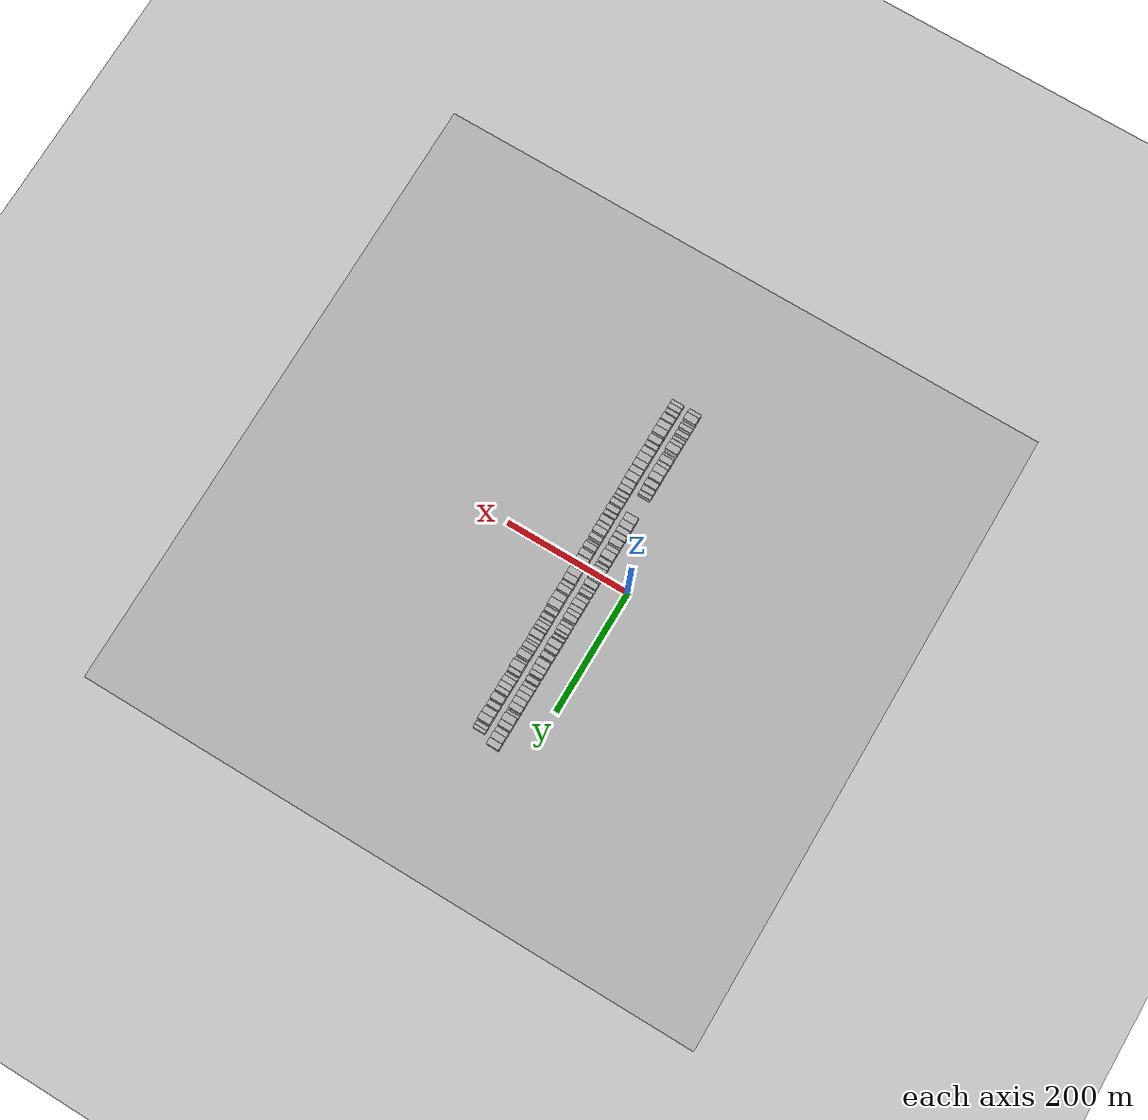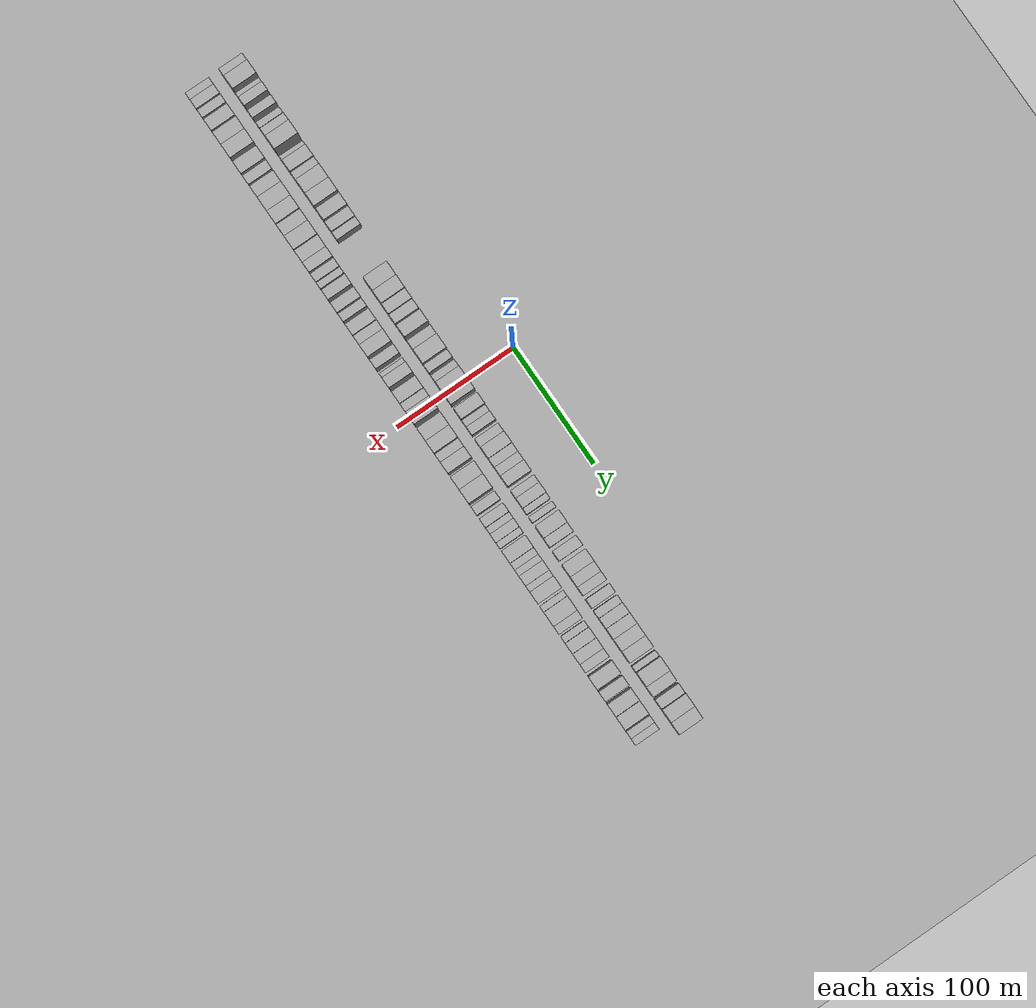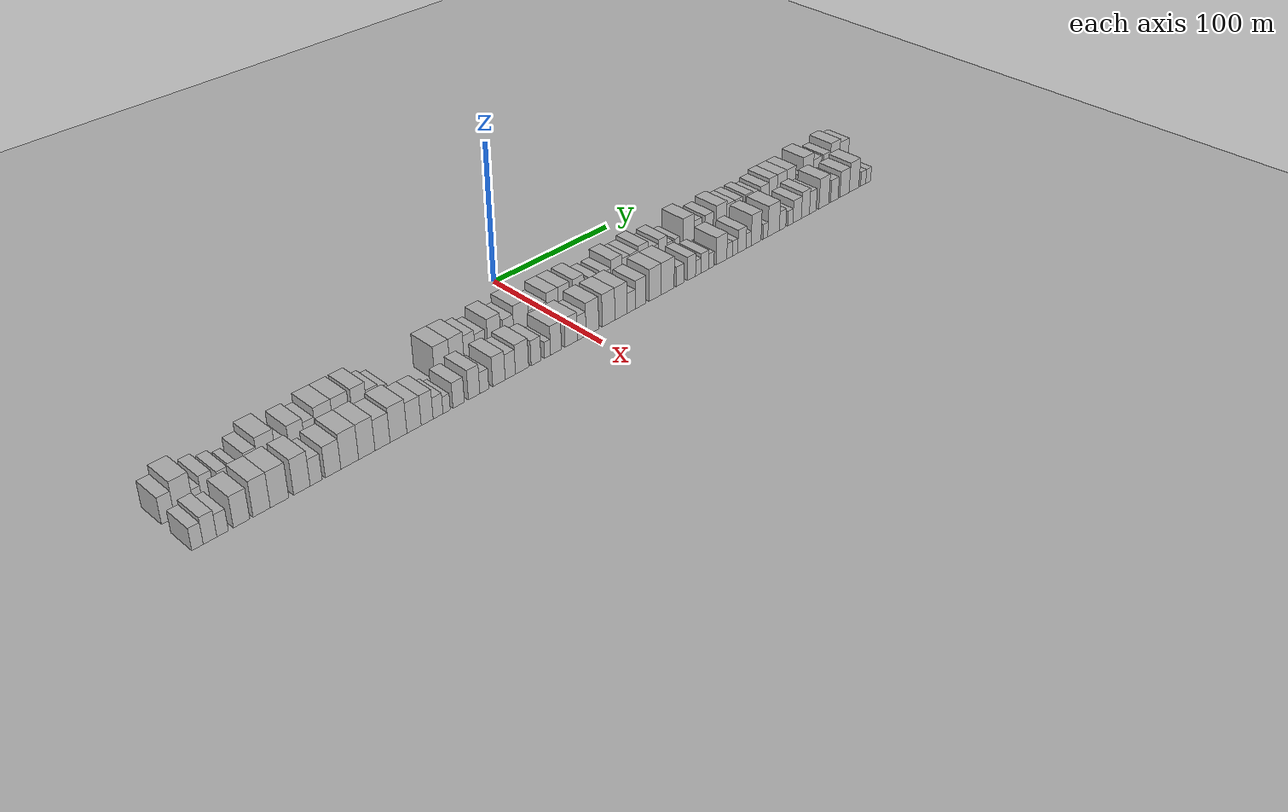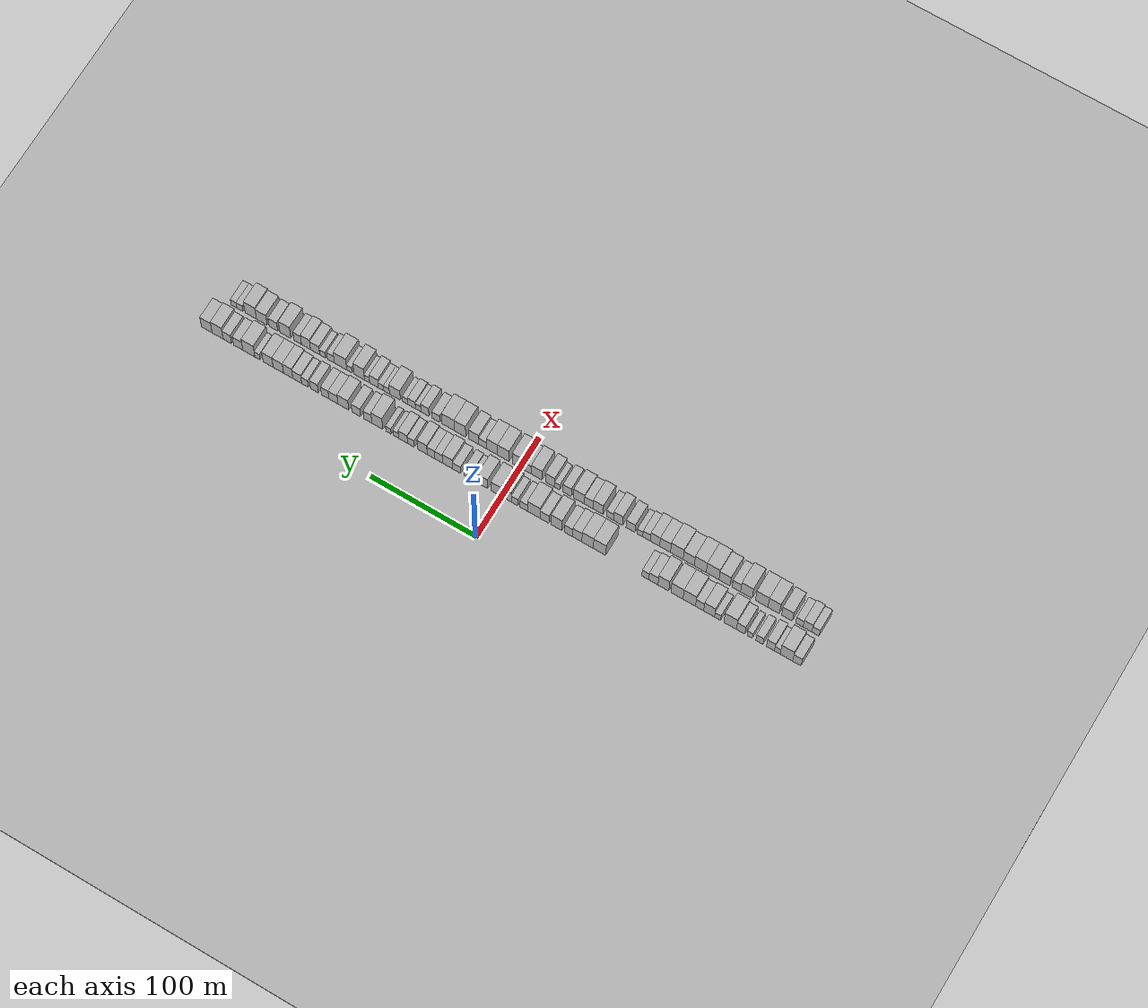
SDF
<?xml version="1.0" encoding="utf-8"?>

<sdf version="1.6">

   <world name="default">

      <gui fullscreen="0">

         <camera name="user_camera">

            <pose>-15 0 4.57585 0 0 0</pose>

            <view_controller>orbit</view_controller>

         </camera>

      </gui>

      <scene>

         <sky>

           <clouds>

             <speed>12</speed>

           </clouds>

         </sky>

         <ambient>0.4 0.4 0.4 1</ambient>

         <background>0.7 0.7 0.7 1</background>

         <shadows>1</shadows>

      </scene>

      <gravity>0 0 -9.8066</gravity>

      <magnetic_field>6e-06 2.3e-05 -4.2e-05</magnetic_field>

      <physics default="0" name="default_physics" type="ode">

         <ode>

            <solver>

               <type>quick</type>

               <iters>10</iters>

               <sor>1.0</sor>

               <use_dynamic_moi_rescaling>0</use_dynamic_moi_rescaling>

            </solver>

            <constraints>

               <cfm>0</cfm>

               <erp>0.2</erp>

               <contact_max_correcting_vel>100</contact_max_correcting_vel>

               <contact_surface_layer>0.001</contact_surface_layer>

            </constraints>

         </ode>

         <max_step_size>0.004</max_step_size>

         <real_time_factor>1</real_time_factor>

         <real_time_update_rate>250</real_time_update_rate>

      </physics>

      <light name="sun" type="directional">

         <cast_shadows>1</cast_shadows>

         <pose>0 0 10 0 0 0</pose>

         <diffuse>0.8 0.8 0.8 1</diffuse>

         <specular>0.2 0.2 0.2 1</specular>

         <attenuation>

            <range>1000</range>

            <constant>0.9</constant>

            <linear>0.01</linear>

            <quadratic>0.001</quadratic>

         </attenuation>

         <direction>-0.5 0.1 -0.9</direction>

      </light>

      <include>

         <name>ground_plane_1</name>

         <uri>model://HANNAS_ground_plane</uri>

         <pose>0 0 0  0 0 0</pose>

      </include>

      <include>

         <name>ground_plane_2</name>

         <uri>model://HANNAS_ground_plane</uri>

         <pose>100 0 0  0 0 0</pose>

      </include>

      <model name="building_1">

         <static>1</static>

         <pose frame="">50.0000 -274.0984 0 0.000000 0.000000 0.000000</pose>

         <link name="link">

            <pose frame="">0 0 9.00 0 0 0</pose>

            <collision name="collision">

               <geometry>

                  <box>

                     <size>20.0000 7.8032 18.0000</size>

                  </box>

               </geometry>

               <max_contacts>10</max_contacts>

               <surface>

                  <contact>

                     <ode/>

                  </contact>

                  <bounce/>

                  <friction>

                     <torsional>

                        <ode/>

                     </torsional>

                     <ode/>

                  </friction>

               </surface>

            </collision>

            <visual name="visual">

               <cast_shadows>0</cast_shadows>

               <geometry>

                  <box>

                     <size>20.0000 7.8032 18.0000</size>

                  </box>

               </geometry>

               <material>

                  <script>

                     <uri>model://HANNAS_wall/materials/scripts</uri>

                     <uri>model://HANNAS_wall/materials/textures</uri>

                     <name>vrc/HANNAS_wall</name>

                  </script>

               </material>

            </visual>

            <self_collide>0</self_collide>

            <enable_wind>0</enable_wind>

            <kinematic>0</kinematic>

         </link>

      </model>

      <model name="building_2">

         <static>1</static>

         <pose frame="">50.0000 -264.4991 0 0.000000 0.000000 0.000000</pose>

         <link name="link">

            <pose frame="">0 0 12.00 0 0 0</pose>

            <collision name="collision">

               <geometry>

                  <box>

                     <size>20.0000 11.3953 24.0000</size>

                  </box>

               </geometry>

               <max_contacts>10</max_contacts>

               <surface>

                  <contact>

                     <ode/>

                  </contact>

                  <bounce/>

                  <friction>

                     <torsional>

                        <ode/>

                     </torsional>

                     <ode/>

                  </friction>

               </surface>

            </collision>

            <visual name="visual">

               <cast_shadows>0</cast_shadows>

               <geometry>

                  <box>

                     <size>20.0000 11.3953 24.0000</size>

                  </box>

               </geometry>

               <material>

                  <script>

                     <uri>model://HANNAS_wall/materials/scripts</uri>

                     <uri>model://HANNAS_wall/materials/textures</uri>

                     <name>vrc/HANNAS_wall</name>

                  </script>

               </material>

            </visual>

            <self_collide>0</self_collide>

            <enable_wind>0</enable_wind>

            <kinematic>0</kinematic>

         </link>

      </model>

      <model name="building_3">

         <static>1</static>

         <pose frame="">50.0000 -256.1798 0 0.000000 0.000000 0.000000</pose>

         <link name="link">

            <pose frame="">0 0 6.00 0 0 0</pose>

            <collision name="collision">

               <geometry>

                  <box>

                     <size>20.0000 5.2434 12.0000</size>

                  </box>

               </geometry>

               <max_contacts>10</max_contacts>

               <surface>

                  <contact>

                     <ode/>

                  </contact>

                  <bounce/>

                  <friction>

                     <torsional>

                        <ode/>

                     </torsional>

                     <ode/>

                  </friction>

               </surface>

            </collision>

            <visual name="visual">

               <cast_shadows>0</cast_shadows>

               <geometry>

                  <box>

                     <size>20.0000 5.2434 12.0000</size>

                  </box>

               </geometry>

               <material>

                  <script>

                     <uri>model://HANNAS_wall/materials/scripts</uri>

                     <uri>model://HANNAS_wall/materials/textures</uri>

                     <name>vrc/HANNAS_wall</name>

                  </script>

               </material>

            </visual>

            <self_collide>0</self_collide>

            <enable_wind>0</enable_wind>

            <kinematic>0</kinematic>

         </link>

      </model>

      <model name="building_4">

         <static>1</static>

         <pose frame="">50.0000 -249.8199 0 0.000000 0.000000 0.000000</pose>

         <link name="link">

            <pose frame="">0 0 9.00 0 0 0</pose>

            <collision name="collision">

               <geometry>

                  <box>

                     <size>20.0000 7.4764 18.0000</size>

                  </box>

               </geometry>

               <max_contacts>10</max_contacts>

               <surface>

                  <contact>

                     <ode/>

                  </contact>

                  <bounce/>

                  <friction>

                     <torsional>

                        <ode/>

                     </torsional>

                     <ode/>

                  </friction>

               </surface>

            </collision>

            <visual name="visual">

               <cast_shadows>0</cast_shadows>

               <geometry>

                  <box>

                     <size>20.0000 7.4764 18.0000</size>

                  </box>

               </geometry>

               <material>

                  <script>

                     <uri>model://HANNAS_wall/materials/scripts</uri>

                     <uri>model://HANNAS_wall/materials/textures</uri>

                     <name>vrc/HANNAS_wall</name>

                  </script>

               </material>

            </visual>

            <self_collide>0</self_collide>

            <enable_wind>0</enable_wind>

            <kinematic>0</kinematic>

         </link>

      </model>

      <model name="building_5">

         <static>1</static>

         <pose frame="">50.0000 -239.6976 0 0.000000 0.000000 0.000000</pose>

         <link name="link">

            <pose frame="">0 0 7.50 0 0 0</pose>

            <collision name="collision">

               <geometry>

                  <box>

                     <size>20.0000 6.7683 15.0000</size>

                  </box>

               </geometry>

               <max_contacts>10</max_contacts>

               <surface>

                  <contact>

                     <ode/>

                  </contact>

                  <bounce/>

                  <friction>

                     <torsional>

                        <ode/>

                     </torsional>

                     <ode/>

                  </friction>

               </surface>

            </collision>

            <visual name="visual">

               <cast_shadows>0</cast_shadows>

               <geometry>

                  <box>

                     <size>20.0000 6.7683 15.0000</size>

                  </box>

               </geometry>

               <material>

                  <script>

                     <uri>model://HANNAS_wall/materials/scripts</uri>

                     <uri>model://HANNAS_wall/materials/textures</uri>

                     <name>vrc/HANNAS_wall</name>

                  </script>

               </material>

            </visual>

            <self_collide>0</self_collide>

            <enable_wind>0</enable_wind>

            <kinematic>0</kinematic>

         </link>

      </model>

      <model name="building_6">

         <static>1</static>

         <pose frame="">50.0000 -230.8334 0 0.000000 0.000000 0.000000</pose>

         <link name="link">

            <pose frame="">0 0 6.00 0 0 0</pose>

            <collision name="collision">

               <geometry>

                  <box>

                     <size>20.0000 4.9600 12.0000</size>

                  </box>

               </geometry>

               <max_contacts>10</max_contacts>

               <surface>

                  <contact>

                     <ode/>

                  </contact>

                  <bounce/>

                  <friction>

                     <torsional>

                        <ode/>

                     </torsional>

                     <ode/>

                  </friction>

               </surface>

            </collision>

            <visual name="visual">

               <cast_shadows>0</cast_shadows>

               <geometry>

                  <box>

                     <size>20.0000 4.9600 12.0000</size>

                  </box>

               </geometry>

               <material>

                  <script>

                     <uri>model://HANNAS_wall/materials/scripts</uri>

                     <uri>model://HANNAS_wall/materials/textures</uri>

                     <name>vrc/HANNAS_wall</name>

                  </script>

               </material>

            </visual>

            <self_collide>0</self_collide>

            <enable_wind>0</enable_wind>

            <kinematic>0</kinematic>

         </link>

      </model>

      <model name="building_7">

         <static>1</static>

         <pose frame="">50.0000 -222.4226 0 0.000000 0.000000 0.000000</pose>

         <link name="link">

            <pose frame="">0 0 9.00 0 0 0</pose>

            <collision name="collision">

               <geometry>

                  <box>

                     <size>20.0000 7.8615 18.0000</size>

                  </box>

               </geometry>

               <max_contacts>10</max_contacts>

               <surface>

                  <contact>

                     <ode/>

                  </contact>

                  <bounce/>

                  <friction>

                     <torsional>

                        <ode/>

                     </torsional>

                     <ode/>

                  </friction>

               </surface>

            </collision>

            <visual name="visual">

               <cast_shadows>0</cast_shadows>

               <geometry>

                  <box>

                     <size>20.0000 7.8615 18.0000</size>

                  </box>

               </geometry>

               <material>

                  <script>

                     <uri>model://HANNAS_wall/materials/scripts</uri>

                     <uri>model://HANNAS_wall/materials/textures</uri>

                     <name>vrc/HANNAS_wall</name>

                  </script>

               </material>

            </visual>

            <self_collide>0</self_collide>

            <enable_wind>0</enable_wind>

            <kinematic>0</kinematic>

         </link>

      </model>

      <model name="building_8">

         <static>1</static>

         <pose frame="">50.0000 -212.7386 0 0.000000 0.000000 0.000000</pose>

         <link name="link">

            <pose frame="">0 0 12.00 0 0 0</pose>

            <collision name="collision">

               <geometry>

                  <box>

                     <size>20.0000 11.5064 24.0000</size>

                  </box>

               </geometry>

               <max_contacts>10</max_contacts>

               <surface>

                  <contact>

                     <ode/>

                  </contact>

                  <bounce/>

                  <friction>

                     <torsional>

                        <ode/>

                     </torsional>

                     <ode/>

                  </friction>

               </surface>

            </collision>

            <visual name="visual">

               <cast_shadows>0</cast_shadows>

               <geometry>

                  <box>

                     <size>20.0000 11.5064 24.0000</size>

                  </box>

               </geometry>

               <material>

                  <script>

                     <uri>model://HANNAS_wall/materials/scripts</uri>

                     <uri>model://HANNAS_wall/materials/textures</uri>

                     <name>vrc/HANNAS_wall</name>

                  </script>

               </material>

            </visual>

            <self_collide>0</self_collide>

            <enable_wind>0</enable_wind>

            <kinematic>0</kinematic>

         </link>

      </model>

      <model name="building_9">

         <static>1</static>

         <pose frame="">50.0000 -201.2006 0 0.000000 0.000000 0.000000</pose>

         <link name="link">

            <pose frame="">0 0 6.00 0 0 0</pose>

            <collision name="collision">

               <geometry>

                  <box>

                     <size>20.0000 5.5696 12.0000</size>

                  </box>

               </geometry>

               <max_contacts>10</max_contacts>

               <surface>

                  <contact>

                     <ode/>

                  </contact>

                  <bounce/>

                  <friction>

                     <torsional>

                        <ode/>

                     </torsional>

                     <ode/>

                  </friction>

               </surface>

            </collision>

            <visual name="visual">

               <cast_shadows>0</cast_shadows>

               <geometry>

                  <box>

                     <size>20.0000 5.5696 12.0000</size>

                  </box>

               </geometry>

               <material>

                  <script>

                     <uri>model://HANNAS_wall/materials/scripts</uri>

                     <uri>model://HANNAS_wall/materials/textures</uri>

                     <name>vrc/HANNAS_wall</name>

                  </script>

               </material>

            </visual>

            <self_collide>0</self_collide>

            <enable_wind>0</enable_wind>

            <kinematic>0</kinematic>

         </link>

      </model>

      <model name="building_10">

         <static>1</static>

         <pose frame="">50.0000 -193.3967 0 0.000000 0.000000 0.000000</pose>

         <link name="link">

            <pose frame="">0 0 10.50 0 0 0</pose>

            <collision name="collision">

               <geometry>

                  <box>

                     <size>20.0000 10.0381 21.0000</size>

                  </box>

               </geometry>

               <max_contacts>10</max_contacts>

               <surface>

                  <contact>

                     <ode/>

                  </contact>

                  <bounce/>

                  <friction>

                     <torsional>

                        <ode/>

                     </torsional>

                     <ode/>

                  </friction>

               </surface>

            </collision>

            <visual name="visual">

               <cast_shadows>0</cast_shadows>

               <geometry>

                  <box>

                     <size>20.0000 10.0381 21.0000</size>

                  </box>

               </geometry>

               <material>

                  <script>

                     <uri>model://HANNAS_wall/materials/scripts</uri>

                     <uri>model://HANNAS_wall/materials/textures</uri>

                     <name>vrc/HANNAS_wall</name>

                  </script>

               </material>

            </visual>

            <self_collide>0</self_collide>

            <enable_wind>0</enable_wind>

            <kinematic>0</kinematic>

         </link>

      </model>

      <model name="building_11">

         <static>1</static>

         <pose frame="">50.0000 -184.5823 0 0.000000 0.000000 0.000000</pose>

         <link name="link">

            <pose frame="">0 0 9.00 0 0 0</pose>

            <collision name="collision">

               <geometry>

                  <box>

                     <size>20.0000 7.5908 18.0000</size>

                  </box>

               </geometry>

               <max_contacts>10</max_contacts>

               <surface>

                  <contact>

                     <ode/>

                  </contact>

                  <bounce/>

                  <friction>

                     <torsional>

                        <ode/>

                     </torsional>

                     <ode/>

                  </friction>

               </surface>

            </collision>

            <visual name="visual">

               <cast_shadows>0</cast_shadows>

               <geometry>

                  <box>

                     <size>20.0000 7.5908 18.0000</size>

                  </box>

               </geometry>

               <material>

                  <script>

                     <uri>model://HANNAS_wall/materials/scripts</uri>

                     <uri>model://HANNAS_wall/materials/textures</uri>

                     <name>vrc/HANNAS_wall</name>

                  </script>

               </material>

            </visual>

            <self_collide>0</self_collide>

            <enable_wind>0</enable_wind>

            <kinematic>0</kinematic>

         </link>

      </model>

      <model name="building_12">

         <static>1</static>

         <pose frame="">50.0000 -175.0051 0 0.000000 0.000000 0.000000</pose>

         <link name="link">

            <pose frame="">0 0 12.00 0 0 0</pose>

            <collision name="collision">

               <geometry>

                  <box>

                     <size>20.0000 11.5636 24.0000</size>

                  </box>

               </geometry>

               <max_contacts>10</max_contacts>

               <surface>

                  <contact>

                     <ode/>

                  </contact>

                  <bounce/>

                  <friction>

                     <torsional>

                        <ode/>

                     </torsional>

                     <ode/>

                  </friction>

               </surface>

            </collision>

            <visual name="visual">

               <cast_shadows>0</cast_shadows>

               <geometry>

                  <box>

                     <size>20.0000 11.5636 24.0000</size>

                  </box>

               </geometry>

               <material>

                  <script>

                     <uri>model://HANNAS_wall/materials/scripts</uri>

                     <uri>model://HANNAS_wall/materials/textures</uri>

                     <name>vrc/HANNAS_wall</name>

                  </script>

               </material>

            </visual>

            <self_collide>0</self_collide>

            <enable_wind>0</enable_wind>

            <kinematic>0</kinematic>

         </link>

      </model>

      <model name="building_13">

         <static>1</static>

         <pose frame="">50.0000 -163.6334 0 0.000000 0.000000 0.000000</pose>

         <link name="link">

            <pose frame="">0 0 12.00 0 0 0</pose>

            <collision name="collision">

               <geometry>

                  <box>

                     <size>20.0000 11.1797 24.0000</size>

                  </box>

               </geometry>

               <max_contacts>10</max_contacts>

               <surface>

                  <contact>

                     <ode/>

                  </contact>

                  <bounce/>

                  <friction>

                     <torsional>

                        <ode/>

                     </torsional>

                     <ode/>

                  </friction>

               </surface>

            </collision>

            <visual name="visual">

               <cast_shadows>0</cast_shadows>

               <geometry>

                  <box>

                     <size>20.0000 11.1797 24.0000</size>

                  </box>

               </geometry>

               <material>

                  <script>

                     <uri>model://HANNAS_wall/materials/scripts</uri>

                     <uri>model://HANNAS_wall/materials/textures</uri>

                     <name>vrc/HANNAS_wall</name>

                  </script>

               </material>

            </visual>

            <self_collide>0</self_collide>

            <enable_wind>0</enable_wind>

            <kinematic>0</kinematic>

         </link>

      </model>

      <model name="building_14">

         <static>1</static>

         <pose frame="">50.0000 -151.0319 0 0.000000 0.000000 0.000000</pose>

         <link name="link">

            <pose frame="">0 0 12.00 0 0 0</pose>

            <collision name="collision">

               <geometry>

                  <box>

                     <size>20.0000 10.0233 24.0000</size>

                  </box>

               </geometry>

               <max_contacts>10</max_contacts>

               <surface>

                  <contact>

                     <ode/>

                  </contact>

                  <bounce/>

                  <friction>

                     <torsional>

                        <ode/>

                     </torsional>

                     <ode/>

                  </friction>

               </surface>

            </collision>

            <visual name="visual">

               <cast_shadows>0</cast_shadows>

               <geometry>

                  <box>

                     <size>20.0000 10.0233 24.0000</size>

                  </box>

               </geometry>

               <material>

                  <script>

                     <uri>model://HANNAS_wall/materials/scripts</uri>

                     <uri>model://HANNAS_wall/materials/textures</uri>

                     <name>vrc/HANNAS_wall</name>

                  </script>

               </material>

            </visual>

            <self_collide>0</self_collide>

            <enable_wind>0</enable_wind>

            <kinematic>0</kinematic>

         </link>

      </model>

      <model name="building_15">

         <static>1</static>

         <pose frame="">50.0000 -141.7876 0 0.000000 0.000000 0.000000</pose>

         <link name="link">

            <pose frame="">0 0 9.00 0 0 0</pose>

            <collision name="collision">

               <geometry>

                  <box>

                     <size>20.0000 8.4652 18.0000</size>

                  </box>

               </geometry>

               <max_contacts>10</max_contacts>

               <surface>

                  <contact>

                     <ode/>

                  </contact>

                  <bounce/>

                  <friction>

                     <torsional>

                        <ode/>

                     </torsional>

                     <ode/>

                  </friction>

               </surface>

            </collision>

            <visual name="visual">

               <cast_shadows>0</cast_shadows>

               <geometry>

                  <box>

                     <size>20.0000 8.4652 18.0000</size>

                  </box>

               </geometry>

               <material>

                  <script>

                     <uri>model://HANNAS_wall/materials/scripts</uri>

                     <uri>model://HANNAS_wall/materials/textures</uri>

                     <name>vrc/HANNAS_wall</name>

                  </script>

               </material>

            </visual>

            <self_collide>0</self_collide>

            <enable_wind>0</enable_wind>

            <kinematic>0</kinematic>

         </link>

      </model>

      <model name="building_16">

         <static>1</static>

         <pose frame="">50.0000 -134.3034 0 0.000000 0.000000 0.000000</pose>

         <link name="link">

            <pose frame="">0 0 7.50 0 0 0</pose>

            <collision name="collision">

               <geometry>

                  <box>

                     <size>20.0000 6.5032 15.0000</size>

                  </box>

               </geometry>

               <max_contacts>10</max_contacts>

               <surface>

                  <contact>

                     <ode/>

                  </contact>

                  <bounce/>

                  <friction>

                     <torsional>

                        <ode/>

                     </torsional>

                     <ode/>

                  </friction>

               </surface>

            </collision>

            <visual name="visual">

               <cast_shadows>0</cast_shadows>

               <geometry>

                  <box>

                     <size>20.0000 6.5032 15.0000</size>

                  </box>

               </geometry>

               <material>

                  <script>

                     <uri>model://HANNAS_wall/materials/scripts</uri>

                     <uri>model://HANNAS_wall/materials/textures</uri>

                     <name>vrc/HANNAS_wall</name>

                  </script>

               </material>

            </visual>

            <self_collide>0</self_collide>

            <enable_wind>0</enable_wind>

            <kinematic>0</kinematic>

         </link>

      </model>

      <model name="building_17">

         <static>1</static>

         <pose frame="">50.0000 -91.6437 0 0.000000 0.000000 0.000000</pose>

         <link name="link">

            <pose frame="">0 0 12.00 0 0 0</pose>

            <collision name="collision">

               <geometry>

                  <box>

                     <size>20.0000 11.6054 24.0000</size>

                  </box>

               </geometry>

               <max_contacts>10</max_contacts>

               <surface>

                  <contact>

                     <ode/>

                  </contact>

                  <bounce/>

                  <friction>

                     <torsional>

                        <ode/>

                     </torsional>

                     <ode/>

                  </friction>

               </surface>

            </collision>

            <visual name="visual">

               <cast_shadows>0</cast_shadows>

               <geometry>

                  <box>

                     <size>20.0000 11.6054 24.0000</size>

                  </box>

               </geometry>

               <material>

                  <script>

                     <uri>model://HANNAS_wall/materials/scripts</uri>

                     <uri>model://HANNAS_wall/materials/textures</uri>

                     <name>vrc/HANNAS_wall</name>

                  </script>

               </material>

            </visual>

            <self_collide>0</self_collide>

            <enable_wind>0</enable_wind>

            <kinematic>0</kinematic>

         </link>

      </model>

      <model name="building_18">

         <static>1</static>

         <pose frame="">50.0000 -80.4419 0 0.000000 0.000000 0.000000</pose>

         <link name="link">

            <pose frame="">0 0 12.00 0 0 0</pose>

            <collision name="collision">

               <geometry>

                  <box>

                     <size>20.0000 10.7983 24.0000</size>

                  </box>

               </geometry>

               <max_contacts>10</max_contacts>

               <surface>

                  <contact>

                     <ode/>

                  </contact>

                  <bounce/>

                  <friction>

                     <torsional>

                        <ode/>

                     </torsional>

                     <ode/>

                  </friction>

               </surface>

            </collision>

            <visual name="visual">

               <cast_shadows>0</cast_shadows>

               <geometry>

                  <box>

                     <size>20.0000 10.7983 24.0000</size>

                  </box>

               </geometry>

               <material>

                  <script>

                     <uri>model://HANNAS_wall/materials/scripts</uri>

                     <uri>model://HANNAS_wall/materials/textures</uri>

                     <name>vrc/HANNAS_wall</name>

                  </script>

               </material>

            </visual>

            <self_collide>0</self_collide>

            <enable_wind>0</enable_wind>

            <kinematic>0</kinematic>

         </link>

      </model>

      <model name="building_19">

         <static>1</static>

         <pose frame="">50.0000 -70.7479 0 0.000000 0.000000 0.000000</pose>

         <link name="link">

            <pose frame="">0 0 10.50 0 0 0</pose>

            <collision name="collision">

               <geometry>

                  <box>

                     <size>20.0000 8.5898 21.0000</size>

                  </box>

               </geometry>

               <max_contacts>10</max_contacts>

               <surface>

                  <contact>

                     <ode/>

                  </contact>

                  <bounce/>

                  <friction>

                     <torsional>

                        <ode/>

                     </torsional>

                     <ode/>

                  </friction>

               </surface>

            </collision>

            <visual name="visual">

               <cast_shadows>0</cast_shadows>

               <geometry>

                  <box>

                     <size>20.0000 8.5898 21.0000</size>

                  </box>

               </geometry>

               <material>

                  <script>

                     <uri>model://HANNAS_wall/materials/scripts</uri>

                     <uri>model://HANNAS_wall/materials/textures</uri>

                     <name>vrc/HANNAS_wall</name>

                  </script>

               </material>

            </visual>

            <self_collide>0</self_collide>

            <enable_wind>0</enable_wind>

            <kinematic>0</kinematic>

         </link>

      </model>

      <model name="building_20">

         <static>1</static>

         <pose frame="">50.0000 -62.4788 0 0.000000 0.000000 0.000000</pose>

         <link name="link">

            <pose frame="">0 0 9.00 0 0 0</pose>

            <collision name="collision">

               <geometry>

                  <box>

                     <size>20.0000 7.9483 18.0000</size>

                  </box>

               </geometry>

               <max_contacts>10</max_contacts>

               <surface>

                  <contact>

                     <ode/>

                  </contact>

                  <bounce/>

                  <friction>

                     <torsional>

                        <ode/>

                     </torsional>

                     <ode/>

                  </friction>

               </surface>

            </collision>

            <visual name="visual">

               <cast_shadows>0</cast_shadows>

               <geometry>

                  <box>

                     <size>20.0000 7.9483 18.0000</size>

                  </box>

               </geometry>

               <material>

                  <script>

                     <uri>model://HANNAS_wall/materials/scripts</uri>

                     <uri>model://HANNAS_wall/materials/textures</uri>

                     <name>vrc/HANNAS_wall</name>

                  </script>

               </material>

            </visual>

            <self_collide>0</self_collide>

            <enable_wind>0</enable_wind>

            <kinematic>0</kinematic>

         </link>

      </model>

      <model name="building_21">

         <static>1</static>

         <pose frame="">50.0000 -51.3808 0 0.000000 0.000000 0.000000</pose>

         <link name="link">

            <pose frame="">0 0 12.00 0 0 0</pose>

            <collision name="collision">

               <geometry>

                  <box>

                     <size>20.0000 10.2478 24.0000</size>

                  </box>

               </geometry>

               <max_contacts>10</max_contacts>

               <surface>

                  <contact>

                     <ode/>

                  </contact>

                  <bounce/>

                  <friction>

                     <torsional>

                        <ode/>

                     </torsional>

                     <ode/>

                  </friction>

               </surface>

            </collision>

            <visual name="visual">

               <cast_shadows>0</cast_shadows>

               <geometry>

                  <box>

                     <size>20.0000 10.2478 24.0000</size>

                  </box>

               </geometry>

               <material>

                  <script>

                     <uri>model://HANNAS_wall/materials/scripts</uri>

                     <uri>model://HANNAS_wall/materials/textures</uri>

                     <name>vrc/HANNAS_wall</name>

                  </script>

               </material>

            </visual>

            <self_collide>0</self_collide>

            <enable_wind>0</enable_wind>

            <kinematic>0</kinematic>

         </link>

      </model>

      <model name="building_22">

         <static>1</static>

         <pose frame="">50.0000 -40.0598 0 0.000000 0.000000 0.000000</pose>

         <link name="link">

            <pose frame="">0 0 9.00 0 0 0</pose>

            <collision name="collision">

               <geometry>

                  <box>

                     <size>20.0000 8.3943 18.0000</size>

                  </box>

               </geometry>

               <max_contacts>10</max_contacts>

               <surface>

                  <contact>

                     <ode/>

                  </contact>

                  <bounce/>

                  <friction>

                     <torsional>

                        <ode/>

                     </torsional>

                     <ode/>

                  </friction>

               </surface>

            </collision>

            <visual name="visual">

               <cast_shadows>0</cast_shadows>

               <geometry>

                  <box>

                     <size>20.0000 8.3943 18.0000</size>

                  </box>

               </geometry>

               <material>

                  <script>

                     <uri>model://HANNAS_wall/materials/scripts</uri>

                     <uri>model://HANNAS_wall/materials/textures</uri>

                     <name>vrc/HANNAS_wall</name>

                  </script>

               </material>

            </visual>

            <self_collide>0</self_collide>

            <enable_wind>0</enable_wind>

            <kinematic>0</kinematic>

         </link>

      </model>

      <model name="building_23">

         <static>1</static>

         <pose frame="">50.0000 -29.8732 0 0.000000 0.000000 0.000000</pose>

         <link name="link">

            <pose frame="">0 0 12.00 0 0 0</pose>

            <collision name="collision">

               <geometry>

                  <box>

                     <size>20.0000 11.9789 24.0000</size>

                  </box>

               </geometry>

               <max_contacts>10</max_contacts>

               <surface>

                  <contact>

                     <ode/>

                  </contact>

                  <bounce/>

                  <friction>

                     <torsional>

                        <ode/>

                     </torsional>

                     <ode/>

                  </friction>

               </surface>

            </collision>

            <visual name="visual">

               <cast_shadows>0</cast_shadows>

               <geometry>

                  <box>

                     <size>20.0000 11.9789 24.0000</size>

                  </box>

               </geometry>

               <material>

                  <script>

                     <uri>model://HANNAS_wall/materials/scripts</uri>

                     <uri>model://HANNAS_wall/materials/textures</uri>

                     <name>vrc/HANNAS_wall</name>

                  </script>

               </material>

            </visual>

            <self_collide>0</self_collide>

            <enable_wind>0</enable_wind>

            <kinematic>0</kinematic>

         </link>

      </model>

      <model name="building_24">

         <static>1</static>

         <pose frame="">50.0000 -20.4483 0 0.000000 0.000000 0.000000</pose>

         <link name="link">

            <pose frame="">0 0 7.50 0 0 0</pose>

            <collision name="collision">

               <geometry>

                  <box>

                     <size>20.0000 6.8708 15.0000</size>

                  </box>

               </geometry>

               <max_contacts>10</max_contacts>

               <surface>

                  <contact>

                     <ode/>

                  </contact>

                  <bounce/>

                  <friction>

                     <torsional>

                        <ode/>

                     </torsional>

                     <ode/>

                  </friction>

               </surface>

            </collision>

            <visual name="visual">

               <cast_shadows>0</cast_shadows>

               <geometry>

                  <box>

                     <size>20.0000 6.8708 15.0000</size>

                  </box>

               </geometry>

               <material>

                  <script>

                     <uri>model://HANNAS_wall/materials/scripts</uri>

                     <uri>model://HANNAS_wall/materials/textures</uri>

                     <name>vrc/HANNAS_wall</name>

                  </script>

               </material>

            </visual>

            <self_collide>0</self_collide>

            <enable_wind>0</enable_wind>

            <kinematic>0</kinematic>

         </link>

      </model>

      <model name="building_25">

         <static>1</static>

         <pose frame="">50.0000 -11.8697 0 0.000000 0.000000 0.000000</pose>

         <link name="link">

            <pose frame="">0 0 7.50 0 0 0</pose>

            <collision name="collision">

               <geometry>

                  <box>

                     <size>20.0000 6.2863 15.0000</size>

                  </box>

               </geometry>

               <max_contacts>10</max_contacts>

               <surface>

                  <contact>

                     <ode/>

                  </contact>

                  <bounce/>

                  <friction>

                     <torsional>

                        <ode/>

                     </torsional>

                     <ode/>

                  </friction>

               </surface>

            </collision>

            <visual name="visual">

               <cast_shadows>0</cast_shadows>

               <geometry>

                  <box>

                     <size>20.0000 6.2863 15.0000</size>

                  </box>

               </geometry>

               <material>

                  <script>

                     <uri>model://HANNAS_wall/materials/scripts</uri>

                     <uri>model://HANNAS_wall/materials/textures</uri>

                     <name>vrc/HANNAS_wall</name>

                  </script>

               </material>

            </visual>

            <self_collide>0</self_collide>

            <enable_wind>0</enable_wind>

            <kinematic>0</kinematic>

         </link>

      </model>

      <model name="building_26">

         <static>1</static>

         <pose frame="">50.0000 -3.9226 0 0.000000 0.000000 0.000000</pose>

         <link name="link">

            <pose frame="">0 0 10.50 0 0 0</pose>

            <collision name="collision">

               <geometry>

                  <box>

                     <size>20.0000 9.6079 21.0000</size>

                  </box>

               </geometry>

               <max_contacts>10</max_contacts>

               <surface>

                  <contact>

                     <ode/>

                  </contact>

                  <bounce/>

                  <friction>

                     <torsional>

                        <ode/>

                     </torsional>

                     <ode/>

                  </friction>

               </surface>

            </collision>

            <visual name="visual">

               <cast_shadows>0</cast_shadows>

               <geometry>

                  <box>

                     <size>20.0000 9.6079 21.0000</size>

                  </box>

               </geometry>

               <material>

                  <script>

                     <uri>model://HANNAS_wall/materials/scripts</uri>

                     <uri>model://HANNAS_wall/materials/textures</uri>

                     <name>vrc/HANNAS_wall</name>

                  </script>

               </material>

            </visual>

            <self_collide>0</self_collide>

            <enable_wind>0</enable_wind>

            <kinematic>0</kinematic>

         </link>

      </model>

      <model name="building_27">

         <static>1</static>

         <pose frame="">50.0000 5.7127 0 0.000000 0.000000 0.000000</pose>

         <link name="link">

            <pose frame="">0 0 10.50 0 0 0</pose>

            <collision name="collision">

               <geometry>

                  <box>

                     <size>20.0000 9.6628 21.0000</size>

                  </box>

               </geometry>

               <max_contacts>10</max_contacts>

               <surface>

                  <contact>

                     <ode/>

                  </contact>

                  <bounce/>

                  <friction>

                     <torsional>

                        <ode/>

                     </torsional>

                     <ode/>

                  </friction>

               </surface>

            </collision>

            <visual name="visual">

               <cast_shadows>0</cast_shadows>

               <geometry>

                  <box>

                     <size>20.0000 9.6628 21.0000</size>

                  </box>

               </geometry>

               <material>

                  <script>

                     <uri>model://HANNAS_wall/materials/scripts</uri>

                     <uri>model://HANNAS_wall/materials/textures</uri>

                     <name>vrc/HANNAS_wall</name>

                  </script>

               </material>

            </visual>

            <self_collide>0</self_collide>

            <enable_wind>0</enable_wind>

            <kinematic>0</kinematic>

         </link>

      </model>

      <model name="building_28">

         <static>1</static>

         <pose frame="">50.0000 18.3281 0 0.000000 0.000000 0.000000</pose>

         <link name="link">

            <pose frame="">0 0 10.50 0 0 0</pose>

            <collision name="collision">

               <geometry>

                  <box>

                     <size>20.0000 9.5679 21.0000</size>

                  </box>

               </geometry>

               <max_contacts>10</max_contacts>

               <surface>

                  <contact>

                     <ode/>

                  </contact>

                  <bounce/>

                  <friction>

                     <torsional>

                        <ode/>

                     </torsional>

                     <ode/>

                  </friction>

               </surface>

            </collision>

            <visual name="visual">

               <cast_shadows>0</cast_shadows>

               <geometry>

                  <box>

                     <size>20.0000 9.5679 21.0000</size>

                  </box>

               </geometry>

               <material>

                  <script>

                     <uri>model://HANNAS_wall/materials/scripts</uri>

                     <uri>model://HANNAS_wall/materials/textures</uri>

                     <name>vrc/HANNAS_wall</name>

                  </script>

               </material>

            </visual>

            <self_collide>0</self_collide>

            <enable_wind>0</enable_wind>

            <kinematic>0</kinematic>

         </link>

      </model>

      <model name="building_29">

         <static>1</static>

         <pose frame="">50.0000 26.0019 0 0.000000 0.000000 0.000000</pose>

         <link name="link">

            <pose frame="">0 0 6.00 0 0 0</pose>

            <collision name="collision">

               <geometry>

                  <box>

                     <size>20.0000 5.7797 12.0000</size>

                  </box>

               </geometry>

               <max_contacts>10</max_contacts>

               <surface>

                  <contact>

                     <ode/>

                  </contact>

                  <bounce/>

                  <friction>

                     <torsional>

                        <ode/>

                     </torsional>

                     <ode/>

                  </friction>

               </surface>

            </collision>

            <visual name="visual">

               <cast_shadows>0</cast_shadows>

               <geometry>

                  <box>

                     <size>20.0000 5.7797 12.0000</size>

                  </box>

               </geometry>

               <material>

                  <script>

                     <uri>model://HANNAS_wall/materials/scripts</uri>

                     <uri>model://HANNAS_wall/materials/textures</uri>

                     <name>vrc/HANNAS_wall</name>

                  </script>

               </material>

            </visual>

            <self_collide>0</self_collide>

            <enable_wind>0</enable_wind>

            <kinematic>0</kinematic>

         </link>

      </model>

      <model name="building_30">

         <static>1</static>

         <pose frame="">50.0000 32.5020 0 0.000000 0.000000 0.000000</pose>

         <link name="link">

            <pose frame="">0 0 7.50 0 0 0</pose>

            <collision name="collision">

               <geometry>

                  <box>

                     <size>20.0000 7.2206 15.0000</size>

                  </box>

               </geometry>

               <max_contacts>10</max_contacts>

               <surface>

                  <contact>

                     <ode/>

                  </contact>

                  <bounce/>

                  <friction>

                     <torsional>

                        <ode/>

                     </torsional>

                     <ode/>

                  </friction>

               </surface>

            </collision>

            <visual name="visual">

               <cast_shadows>0</cast_shadows>

               <geometry>

                  <box>

                     <size>20.0000 7.2206 15.0000</size>

                  </box>

               </geometry>

               <material>

                  <script>

                     <uri>model://HANNAS_wall/materials/scripts</uri>

                     <uri>model://HANNAS_wall/materials/textures</uri>

                     <name>vrc/HANNAS_wall</name>

                  </script>

               </material>

            </visual>

            <self_collide>0</self_collide>

            <enable_wind>0</enable_wind>

            <kinematic>0</kinematic>

         </link>

      </model>

      <model name="building_31">

         <static>1</static>

         <pose frame="">50.0000 42.8494 0 0.000000 0.000000 0.000000</pose>

         <link name="link">

            <pose frame="">0 0 7.50 0 0 0</pose>

            <collision name="collision">

               <geometry>

                  <box>

                     <size>20.0000 7.4743 15.0000</size>

                  </box>

               </geometry>

               <max_contacts>10</max_contacts>

               <surface>

                  <contact>

                     <ode/>

                  </contact>

                  <bounce/>

                  <friction>

                     <torsional>

                        <ode/>

                     </torsional>

                     <ode/>

                  </friction>

               </surface>

            </collision>

            <visual name="visual">

               <cast_shadows>0</cast_shadows>

               <geometry>

                  <box>

                     <size>20.0000 7.4743 15.0000</size>

                  </box>

               </geometry>

               <material>

                  <script>

                     <uri>model://HANNAS_wall/materials/scripts</uri>

                     <uri>model://HANNAS_wall/materials/textures</uri>

                     <name>vrc/HANNAS_wall</name>

                  </script>

               </material>

            </visual>

            <self_collide>0</self_collide>

            <enable_wind>0</enable_wind>

            <kinematic>0</kinematic>

         </link>

      </model>

      <model name="building_32">

         <static>1</static>

         <pose frame="">50.0000 51.4524 0 0.000000 0.000000 0.000000</pose>

         <link name="link">

            <pose frame="">0 0 10.50 0 0 0</pose>

            <collision name="collision">

               <geometry>

                  <box>

                     <size>20.0000 9.7316 21.0000</size>

                  </box>

               </geometry>

               <max_contacts>10</max_contacts>

               <surface>

                  <contact>

                     <ode/>

                  </contact>

                  <bounce/>

                  <friction>

                     <torsional>

                        <ode/>

                     </torsional>

                     <ode/>

                  </friction>

               </surface>

            </collision>

            <visual name="visual">

               <cast_shadows>0</cast_shadows>

               <geometry>

                  <box>

                     <size>20.0000 9.7316 21.0000</size>

                  </box>

               </geometry>

               <material>

                  <script>

                     <uri>model://HANNAS_wall/materials/scripts</uri>

                     <uri>model://HANNAS_wall/materials/textures</uri>

                     <name>vrc/HANNAS_wall</name>

                  </script>

               </material>

            </visual>

            <self_collide>0</self_collide>

            <enable_wind>0</enable_wind>

            <kinematic>0</kinematic>

         </link>

      </model>

      <model name="building_33">

         <static>1</static>

         <pose frame="">50.0000 59.9531 0 0.000000 0.000000 0.000000</pose>

         <link name="link">

            <pose frame="">0 0 9.00 0 0 0</pose>

            <collision name="collision">

               <geometry>

                  <box>

                     <size>20.0000 7.2698 18.0000</size>

                  </box>

               </geometry>

               <max_contacts>10</max_contacts>

               <surface>

                  <contact>

                     <ode/>

                  </contact>

                  <bounce/>

                  <friction>

                     <torsional>

                        <ode/>

                     </torsional>

                     <ode/>

                  </friction>

               </surface>

            </collision>

            <visual name="visual">

               <cast_shadows>0</cast_shadows>

               <geometry>

                  <box>

                     <size>20.0000 7.2698 18.0000</size>

                  </box>

               </geometry>

               <material>

                  <script>

                     <uri>model://HANNAS_wall/materials/scripts</uri>

                     <uri>model://HANNAS_wall/materials/textures</uri>

                     <name>vrc/HANNAS_wall</name>

                  </script>

               </material>

            </visual>

            <self_collide>0</self_collide>

            <enable_wind>0</enable_wind>

            <kinematic>0</kinematic>

         </link>

      </model>

      <model name="building_34">

         <static>1</static>

         <pose frame="">50.0000 67.2421 0 0.000000 0.000000 0.000000</pose>

         <link name="link">

            <pose frame="">0 0 9.00 0 0 0</pose>

            <collision name="collision">

               <geometry>

                  <box>

                     <size>20.0000 7.3082 18.0000</size>

                  </box>

               </geometry>

               <max_contacts>10</max_contacts>

               <surface>

                  <contact>

                     <ode/>

                  </contact>

                  <bounce/>

                  <friction>

                     <torsional>

                        <ode/>

                     </torsional>

                     <ode/>

                  </friction>

               </surface>

            </collision>

            <visual name="visual">

               <cast_shadows>0</cast_shadows>

               <geometry>

                  <box>

                     <size>20.0000 7.3082 18.0000</size>

                  </box>

               </geometry>

               <material>

                  <script>

                     <uri>model://HANNAS_wall/materials/scripts</uri>

                     <uri>model://HANNAS_wall/materials/textures</uri>

                     <name>vrc/HANNAS_wall</name>

                  </script>

               </material>

            </visual>

            <self_collide>0</self_collide>

            <enable_wind>0</enable_wind>

            <kinematic>0</kinematic>

         </link>

      </model>

      <model name="building_35">

         <static>1</static>

         <pose frame="">50.0000 75.4865 0 0.000000 0.000000 0.000000</pose>

         <link name="link">

            <pose frame="">0 0 10.50 0 0 0</pose>

            <collision name="collision">

               <geometry>

                  <box>

                     <size>20.0000 9.1805 21.0000</size>

                  </box>

               </geometry>

               <max_contacts>10</max_contacts>

               <surface>

                  <contact>

                     <ode/>

                  </contact>

                  <bounce/>

                  <friction>

                     <torsional>

                        <ode/>

                     </torsional>

                     <ode/>

                  </friction>

               </surface>

            </collision>

            <visual name="visual">

               <cast_shadows>0</cast_shadows>

               <geometry>

                  <box>

                     <size>20.0000 9.1805 21.0000</size>

                  </box>

               </geometry>

               <material>

                  <script>

                     <uri>model://HANNAS_wall/materials/scripts</uri>

                     <uri>model://HANNAS_wall/materials/textures</uri>

                     <name>vrc/HANNAS_wall</name>

                  </script>

               </material>

            </visual>

            <self_collide>0</self_collide>

            <enable_wind>0</enable_wind>

            <kinematic>0</kinematic>

         </link>

      </model>

      <model name="building_36">

         <static>1</static>

         <pose frame="">50.0000 86.3893 0 0.000000 0.000000 0.000000</pose>

         <link name="link">

            <pose frame="">0 0 7.50 0 0 0</pose>

            <collision name="collision">

               <geometry>

                  <box>

                     <size>20.0000 6.6253 15.0000</size>

                  </box>

               </geometry>

               <max_contacts>10</max_contacts>

               <surface>

                  <contact>

                     <ode/>

                  </contact>

                  <bounce/>

                  <friction>

                     <torsional>

                        <ode/>

                     </torsional>

                     <ode/>

                  </friction>

               </surface>

            </collision>

            <visual name="visual">

               <cast_shadows>0</cast_shadows>

               <geometry>

                  <box>

                     <size>20.0000 6.6253 15.0000</size>

                  </box>

               </geometry>

               <material>

                  <script>

                     <uri>model://HANNAS_wall/materials/scripts</uri>

                     <uri>model://HANNAS_wall/materials/textures</uri>

                     <name>vrc/HANNAS_wall</name>

                  </script>

               </material>

            </visual>

            <self_collide>0</self_collide>

            <enable_wind>0</enable_wind>

            <kinematic>0</kinematic>

         </link>

      </model>

      <model name="building_37">

         <static>1</static>

         <pose frame="">50.0000 93.9520 0 0.000000 0.000000 0.000000</pose>

         <link name="link">

            <pose frame="">0 0 9.00 0 0 0</pose>

            <collision name="collision">

               <geometry>

                  <box>

                     <size>20.0000 8.5001 18.0000</size>

                  </box>

               </geometry>

               <max_contacts>10</max_contacts>

               <surface>

                  <contact>

                     <ode/>

                  </contact>

                  <bounce/>

                  <friction>

                     <torsional>

                        <ode/>

                     </torsional>

                     <ode/>

                  </friction>

               </surface>

            </collision>

            <visual name="visual">

               <cast_shadows>0</cast_shadows>

               <geometry>

                  <box>

                     <size>20.0000 8.5001 18.0000</size>

                  </box>

               </geometry>

               <material>

                  <script>

                     <uri>model://HANNAS_wall/materials/scripts</uri>

                     <uri>model://HANNAS_wall/materials/textures</uri>

                     <name>vrc/HANNAS_wall</name>

                  </script>

               </material>

            </visual>

            <self_collide>0</self_collide>

            <enable_wind>0</enable_wind>

            <kinematic>0</kinematic>

         </link>

      </model>

      <model name="building_38">

         <static>1</static>

         <pose frame="">50.0000 100.7623 0 0.000000 0.000000 0.000000</pose>

         <link name="link">

            <pose frame="">0 0 6.00 0 0 0</pose>

            <collision name="collision">

               <geometry>

                  <box>

                     <size>20.0000 5.1205 12.0000</size>

                  </box>

               </geometry>

               <max_contacts>10</max_contacts>

               <surface>

                  <contact>

                     <ode/>

                  </contact>

                  <bounce/>

                  <friction>

                     <torsional>

                        <ode/>

                     </torsional>

                     <ode/>

                  </friction>

               </surface>

            </collision>

            <visual name="visual">

               <cast_shadows>0</cast_shadows>

               <geometry>

                  <box>

                     <size>20.0000 5.1205 12.0000</size>

                  </box>

               </geometry>

               <material>

                  <script>

                     <uri>model://HANNAS_wall/materials/scripts</uri>

                     <uri>model://HANNAS_wall/materials/textures</uri>

                     <name>vrc/HANNAS_wall</name>

                  </script>

               </material>

            </visual>

            <self_collide>0</self_collide>

            <enable_wind>0</enable_wind>

            <kinematic>0</kinematic>

         </link>

      </model>

      <model name="building_39">

         <static>1</static>

         <pose frame="">50.0000 107.8391 0 0.000000 0.000000 0.000000</pose>

         <link name="link">

            <pose frame="">0 0 6.00 0 0 0</pose>

            <collision name="collision">

               <geometry>

                  <box>

                     <size>20.0000 5.0329 12.0000</size>

                  </box>

               </geometry>

               <max_contacts>10</max_contacts>

               <surface>

                  <contact>

                     <ode/>

                  </contact>

                  <bounce/>

                  <friction>

                     <torsional>

                        <ode/>

                     </torsional>

                     <ode/>

                  </friction>

               </surface>

            </collision>

            <visual name="visual">

               <cast_shadows>0</cast_shadows>

               <geometry>

                  <box>

                     <size>20.0000 5.0329 12.0000</size>

                  </box>

               </geometry>

               <material>

                  <script>

                     <uri>model://HANNAS_wall/materials/scripts</uri>

                     <uri>model://HANNAS_wall/materials/textures</uri>

                     <name>vrc/HANNAS_wall</name>

                  </script>

               </material>

            </visual>

            <self_collide>0</self_collide>

            <enable_wind>0</enable_wind>

            <kinematic>0</kinematic>

         </link>

      </model>

      <model name="building_40">

         <static>1</static>

         <pose frame="">50.0000 118.5804 0 0.000000 0.000000 0.000000</pose>

         <link name="link">

            <pose frame="">0 0 12.00 0 0 0</pose>

            <collision name="collision">

               <geometry>

                  <box>

                     <size>20.0000 10.4498 24.0000</size>

                  </box>

               </geometry>

               <max_contacts>10</max_contacts>

               <surface>

                  <contact>

                     <ode/>

                  </contact>

                  <bounce/>

                  <friction>

                     <torsional>

                        <ode/>

                     </torsional>

                     <ode/>

                  </friction>

               </surface>

            </collision>

            <visual name="visual">

               <cast_shadows>0</cast_shadows>

               <geometry>

                  <box>

                     <size>20.0000 10.4498 24.0000</size>

                  </box>

               </geometry>

               <material>

                  <script>

                     <uri>model://HANNAS_wall/materials/scripts</uri>

                     <uri>model://HANNAS_wall/materials/textures</uri>

                     <name>vrc/HANNAS_wall</name>

                  </script>

               </material>

            </visual>

            <self_collide>0</self_collide>

            <enable_wind>0</enable_wind>

            <kinematic>0</kinematic>

         </link>

      </model>

      <model name="building_41">

         <static>1</static>

         <pose frame="">50.0000 127.6384 0 0.000000 0.000000 0.000000</pose>

         <link name="link">

            <pose frame="">0 0 9.00 0 0 0</pose>

            <collision name="collision">

               <geometry>

                  <box>

                     <size>20.0000 7.6661 18.0000</size>

                  </box>

               </geometry>

               <max_contacts>10</max_contacts>

               <surface>

                  <contact>

                     <ode/>

                  </contact>

                  <bounce/>

                  <friction>

                     <torsional>

                        <ode/>

                     </torsional>

                     <ode/>

                  </friction>

               </surface>

            </collision>

            <visual name="visual">

               <cast_shadows>0</cast_shadows>

               <geometry>

                  <box>

                     <size>20.0000 7.6661 18.0000</size>

                  </box>

               </geometry>

               <material>

                  <script>

                     <uri>model://HANNAS_wall/materials/scripts</uri>

                     <uri>model://HANNAS_wall/materials/textures</uri>

                     <name>vrc/HANNAS_wall</name>

                  </script>

               </material>

            </visual>

            <self_collide>0</self_collide>

            <enable_wind>0</enable_wind>

            <kinematic>0</kinematic>

         </link>

      </model>

      <model name="building_42">

         <static>1</static>

         <pose frame="">50.0000 138.7081 0 0.000000 0.000000 0.000000</pose>

         <link name="link">

            <pose frame="">0 0 9.00 0 0 0</pose>

            <collision name="collision">

               <geometry>

                  <box>

                     <size>20.0000 8.4734 18.0000</size>

                  </box>

               </geometry>

               <max_contacts>10</max_contacts>

               <surface>

                  <contact>

                     <ode/>

                  </contact>

                  <bounce/>

                  <friction>

                     <torsional>

                        <ode/>

                     </torsional>

                     <ode/>

                  </friction>

               </surface>

            </collision>

            <visual name="visual">

               <cast_shadows>0</cast_shadows>

               <geometry>

                  <box>

                     <size>20.0000 8.4734 18.0000</size>

                  </box>

               </geometry>

               <material>

                  <script>

                     <uri>model://HANNAS_wall/materials/scripts</uri>

                     <uri>model://HANNAS_wall/materials/textures</uri>

                     <name>vrc/HANNAS_wall</name>

                  </script>

               </material>

            </visual>

            <self_collide>0</self_collide>

            <enable_wind>0</enable_wind>

            <kinematic>0</kinematic>

         </link>

      </model>

      <model name="building_43">

         <static>1</static>

         <pose frame="">50.0000 151.1465 0 0.000000 0.000000 0.000000</pose>

         <link name="link">

            <pose frame="">0 0 10.50 0 0 0</pose>

            <collision name="collision">

               <geometry>

                  <box>

                     <size>20.0000 10.4034 21.0000</size>

                  </box>

               </geometry>

               <max_contacts>10</max_contacts>

               <surface>

                  <contact>

                     <ode/>

                  </contact>

                  <bounce/>

                  <friction>

                     <torsional>

                        <ode/>

                     </torsional>

                     <ode/>

                  </friction>

               </surface>

            </collision>

            <visual name="visual">

               <cast_shadows>0</cast_shadows>

               <geometry>

                  <box>

                     <size>20.0000 10.4034 21.0000</size>

                  </box>

               </geometry>

               <material>

                  <script>

                     <uri>model://HANNAS_wall/materials/scripts</uri>

                     <uri>model://HANNAS_wall/materials/textures</uri>

                     <name>vrc/HANNAS_wall</name>

                  </script>

               </material>

            </visual>

            <self_collide>0</self_collide>

            <enable_wind>0</enable_wind>

            <kinematic>0</kinematic>

         </link>

      </model>

      <model name="building_44">

         <static>1</static>

         <pose frame="">50.0000 160.6406 0 0.000000 0.000000 0.000000</pose>

         <link name="link">

            <pose frame="">0 0 9.00 0 0 0</pose>

            <collision name="collision">

               <geometry>

                  <box>

                     <size>20.0000 8.5848 18.0000</size>

                  </box>

               </geometry>

               <max_contacts>10</max_contacts>

               <surface>

                  <contact>

                     <ode/>

                  </contact>

                  <bounce/>

                  <friction>

                     <torsional>

                        <ode/>

                     </torsional>

                     <ode/>

                  </friction>

               </surface>

            </collision>

            <visual name="visual">

               <cast_shadows>0</cast_shadows>

               <geometry>

                  <box>

                     <size>20.0000 8.5848 18.0000</size>

                  </box>

               </geometry>

               <material>

                  <script>

                     <uri>model://HANNAS_wall/materials/scripts</uri>

                     <uri>model://HANNAS_wall/materials/textures</uri>

                     <name>vrc/HANNAS_wall</name>

                  </script>

               </material>

            </visual>

            <self_collide>0</self_collide>

            <enable_wind>0</enable_wind>

            <kinematic>0</kinematic>

         </link>

      </model>

      <model name="building_45">

         <static>1</static>

         <pose frame="">50.0000 168.5676 0 0.000000 0.000000 0.000000</pose>

         <link name="link">

            <pose frame="">0 0 9.00 0 0 0</pose>

            <collision name="collision">

               <geometry>

                  <box>

                     <size>20.0000 7.2692 18.0000</size>

                  </box>

               </geometry>

               <max_contacts>10</max_contacts>

               <surface>

                  <contact>

                     <ode/>

                  </contact>

                  <bounce/>

                  <friction>

                     <torsional>

                        <ode/>

                     </torsional>

                     <ode/>

                  </friction>

               </surface>

            </collision>

            <visual name="visual">

               <cast_shadows>0</cast_shadows>

               <geometry>

                  <box>

                     <size>20.0000 7.2692 18.0000</size>

                  </box>

               </geometry>

               <material>

                  <script>

                     <uri>model://HANNAS_wall/materials/scripts</uri>

                     <uri>model://HANNAS_wall/materials/textures</uri>

                     <name>vrc/HANNAS_wall</name>

                  </script>

               </material>

            </visual>

            <self_collide>0</self_collide>

            <enable_wind>0</enable_wind>

            <kinematic>0</kinematic>

         </link>

      </model>

      <model name="building_46">

         <static>1</static>

         <pose frame="">50.0000 179.0036 0 0.000000 0.000000 0.000000</pose>

         <link name="link">

            <pose frame="">0 0 9.00 0 0 0</pose>

            <collision name="collision">

               <geometry>

                  <box>

                     <size>20.0000 7.6027 18.0000</size>

                  </box>

               </geometry>

               <max_contacts>10</max_contacts>

               <surface>

                  <contact>

                     <ode/>

                  </contact>

                  <bounce/>

                  <friction>

                     <torsional>

                        <ode/>

                     </torsional>

                     <ode/>

                  </friction>

               </surface>

            </collision>

            <visual name="visual">

               <cast_shadows>0</cast_shadows>

               <geometry>

                  <box>

                     <size>20.0000 7.6027 18.0000</size>

                  </box>

               </geometry>

               <material>

                  <script>

                     <uri>model://HANNAS_wall/materials/scripts</uri>

                     <uri>model://HANNAS_wall/materials/textures</uri>

                     <name>vrc/HANNAS_wall</name>

                  </script>

               </material>

            </visual>

            <self_collide>0</self_collide>

            <enable_wind>0</enable_wind>

            <kinematic>0</kinematic>

         </link>

      </model>

      <model name="building_47">

         <static>1</static>

         <pose frame="">50.0000 188.0357 0 0.000000 0.000000 0.000000</pose>

         <link name="link">

            <pose frame="">0 0 7.50 0 0 0</pose>

            <collision name="collision">

               <geometry>

                  <box>

                     <size>20.0000 6.4615 15.0000</size>

                  </box>

               </geometry>

               <max_contacts>10</max_contacts>

               <surface>

                  <contact>

                     <ode/>

                  </contact>

                  <bounce/>

                  <friction>

                     <torsional>

                        <ode/>

                     </torsional>

                     <ode/>

                  </friction>

               </surface>

            </collision>

            <visual name="visual">

               <cast_shadows>0</cast_shadows>

               <geometry>

                  <box>

                     <size>20.0000 6.4615 15.0000</size>

                  </box>

               </geometry>

               <material>

                  <script>

                     <uri>model://HANNAS_wall/materials/scripts</uri>

                     <uri>model://HANNAS_wall/materials/textures</uri>

                     <name>vrc/HANNAS_wall</name>

                  </script>

               </material>

            </visual>

            <self_collide>0</self_collide>

            <enable_wind>0</enable_wind>

            <kinematic>0</kinematic>

         </link>

      </model>

      <model name="building_48">

         <static>1</static>

         <pose frame="">50.0000 195.5984 0 0.000000 0.000000 0.000000</pose>

         <link name="link">

            <pose frame="">0 0 9.00 0 0 0</pose>

            <collision name="collision">

               <geometry>

                  <box>

                     <size>20.0000 8.6639 18.0000</size>

                  </box>

               </geometry>

               <max_contacts>10</max_contacts>

               <surface>

                  <contact>

                     <ode/>

                  </contact>

                  <bounce/>

                  <friction>

                     <torsional>

                        <ode/>

                     </torsional>

                     <ode/>

                  </friction>

               </surface>

            </collision>

            <visual name="visual">

               <cast_shadows>0</cast_shadows>

               <geometry>

                  <box>

                     <size>20.0000 8.6639 18.0000</size>

                  </box>

               </geometry>

               <material>

                  <script>

                     <uri>model://HANNAS_wall/materials/scripts</uri>

                     <uri>model://HANNAS_wall/materials/textures</uri>

                     <name>vrc/HANNAS_wall</name>

                  </script>

               </material>

            </visual>

            <self_collide>0</self_collide>

            <enable_wind>0</enable_wind>

            <kinematic>0</kinematic>

         </link>

      </model>

      <model name="building_49">

         <static>1</static>

         <pose frame="">50.0000 204.3596 0 0.000000 0.000000 0.000000</pose>

         <link name="link">

            <pose frame="">0 0 10.50 0 0 0</pose>

            <collision name="collision">

               <geometry>

                  <box>

                     <size>20.0000 8.8585 21.0000</size>

                  </box>

               </geometry>

               <max_contacts>10</max_contacts>

               <surface>

                  <contact>

                     <ode/>

                  </contact>

                  <bounce/>

                  <friction>

                     <torsional>

                        <ode/>

                     </torsional>

                     <ode/>

                  </friction>

               </surface>

            </collision>

            <visual name="visual">

               <cast_shadows>0</cast_shadows>

               <geometry>

                  <box>

                     <size>20.0000 8.8585 21.0000</size>

                  </box>

               </geometry>

               <material>

                  <script>

                     <uri>model://HANNAS_wall/materials/scripts</uri>

                     <uri>model://HANNAS_wall/materials/textures</uri>

                     <name>vrc/HANNAS_wall</name>

                  </script>

               </material>

            </visual>

            <self_collide>0</self_collide>

            <enable_wind>0</enable_wind>

            <kinematic>0</kinematic>

         </link>

      </model>

      <model name="building_50">

         <static>1</static>

         <pose frame="">50.0000 213.8407 0 0.000000 0.000000 0.000000</pose>

         <link name="link">

            <pose frame="">0 0 10.50 0 0 0</pose>

            <collision name="collision">

               <geometry>

                  <box>

                     <size>20.0000 10.1037 21.0000</size>

                  </box>

               </geometry>

               <max_contacts>10</max_contacts>

               <surface>

                  <contact>

                     <ode/>

                  </contact>

                  <bounce/>

                  <friction>

                     <torsional>

                        <ode/>

                     </torsional>

                     <ode/>

                  </friction>

               </surface>

            </collision>

            <visual name="visual">

               <cast_shadows>0</cast_shadows>

               <geometry>

                  <box>

                     <size>20.0000 10.1037 21.0000</size>

                  </box>

               </geometry>

               <material>

                  <script>

                     <uri>model://HANNAS_wall/materials/scripts</uri>

                     <uri>model://HANNAS_wall/materials/textures</uri>

                     <name>vrc/HANNAS_wall</name>

                  </script>

               </material>

            </visual>

            <self_collide>0</self_collide>

            <enable_wind>0</enable_wind>

            <kinematic>0</kinematic>

         </link>

      </model>

      <model name="building_51">

         <static>1</static>

         <pose frame="">50.0000 223.7538 0 0.000000 0.000000 0.000000</pose>

         <link name="link">

            <pose frame="">0 0 10.50 0 0 0</pose>

            <collision name="collision">

               <geometry>

                  <box>

                     <size>20.0000 9.7225 21.0000</size>

                  </box>

               </geometry>

               <max_contacts>10</max_contacts>

               <surface>

                  <contact>

                     <ode/>

                  </contact>

                  <bounce/>

                  <friction>

                     <torsional>

                        <ode/>

                     </torsional>

                     <ode/>

                  </friction>

               </surface>

            </collision>

            <visual name="visual">

               <cast_shadows>0</cast_shadows>

               <geometry>

                  <box>

                     <size>20.0000 9.7225 21.0000</size>

                  </box>

               </geometry>

               <material>

                  <script>

                     <uri>model://HANNAS_wall/materials/scripts</uri>

                     <uri>model://HANNAS_wall/materials/textures</uri>

                     <name>vrc/HANNAS_wall</name>

                  </script>

               </material>

            </visual>

            <self_collide>0</self_collide>

            <enable_wind>0</enable_wind>

            <kinematic>0</kinematic>

         </link>

      </model>

      <model name="building_52">

         <static>1</static>

         <pose frame="">50.0000 234.0645 0 0.000000 0.000000 0.000000</pose>

         <link name="link">

            <pose frame="">0 0 6.00 0 0 0</pose>

            <collision name="collision">

               <geometry>

                  <box>

                     <size>20.0000 4.8989 12.0000</size>

                  </box>

               </geometry>

               <max_contacts>10</max_contacts>

               <surface>

                  <contact>

                     <ode/>

                  </contact>

                  <bounce/>

                  <friction>

                     <torsional>

                        <ode/>

                     </torsional>

                     <ode/>

                  </friction>

               </surface>

            </collision>

            <visual name="visual">

               <cast_shadows>0</cast_shadows>

               <geometry>

                  <box>

                     <size>20.0000 4.8989 12.0000</size>

                  </box>

               </geometry>

               <material>

                  <script>

                     <uri>model://HANNAS_wall/materials/scripts</uri>

                     <uri>model://HANNAS_wall/materials/textures</uri>

                     <name>vrc/HANNAS_wall</name>

                  </script>

               </material>

            </visual>

            <self_collide>0</self_collide>

            <enable_wind>0</enable_wind>

            <kinematic>0</kinematic>

         </link>

      </model>

      <model name="building_53">

         <static>1</static>

         <pose frame="">50.0000 242.3845 0 0.000000 0.000000 0.000000</pose>

         <link name="link">

            <pose frame="">0 0 12.00 0 0 0</pose>

            <collision name="collision">

               <geometry>

                  <box>

                     <size>20.0000 11.7411 24.0000</size>

                  </box>

               </geometry>

               <max_contacts>10</max_contacts>

               <surface>

                  <contact>

                     <ode/>

                  </contact>

                  <bounce/>

                  <friction>

                     <torsional>

                        <ode/>

                     </torsional>

                     <ode/>

                  </friction>

               </surface>

            </collision>

            <visual name="visual">

               <cast_shadows>0</cast_shadows>

               <geometry>

                  <box>

                     <size>20.0000 11.7411 24.0000</size>

                  </box>

               </geometry>

               <material>

                  <script>

                     <uri>model://HANNAS_wall/materials/scripts</uri>

                     <uri>model://HANNAS_wall/materials/textures</uri>

                     <name>vrc/HANNAS_wall</name>

                  </script>

               </material>

            </visual>

            <self_collide>0</self_collide>

            <enable_wind>0</enable_wind>

            <kinematic>0</kinematic>

         </link>

      </model>

      <model name="building_54">

         <static>1</static>

         <pose frame="">50.0000 252.7327 0 0.000000 0.000000 0.000000</pose>

         <link name="link">

            <pose frame="">0 0 9.00 0 0 0</pose>

            <collision name="collision">

               <geometry>

                  <box>

                     <size>20.0000 8.9555 18.0000</size>

                  </box>

               </geometry>

               <max_contacts>10</max_contacts>

               <surface>

                  <contact>

                     <ode/>

                  </contact>

                  <bounce/>

                  <friction>

                     <torsional>

                        <ode/>

                     </torsional>

                     <ode/>

                  </friction>

               </surface>

            </collision>

            <visual name="visual">

               <cast_shadows>0</cast_shadows>

               <geometry>

                  <box>

                     <size>20.0000 8.9555 18.0000</size>

                  </box>

               </geometry>

               <material>

                  <script>

                     <uri>model://HANNAS_wall/materials/scripts</uri>

                     <uri>model://HANNAS_wall/materials/textures</uri>

                     <name>vrc/HANNAS_wall</name>

                  </script>

               </material>

            </visual>

            <self_collide>0</self_collide>

            <enable_wind>0</enable_wind>

            <kinematic>0</kinematic>

         </link>

      </model>

      <model name="building_55">

         <static>1</static>

         <pose frame="">50.0000 263.2553 0 0.000000 0.000000 0.000000</pose>

         <link name="link">

            <pose frame="">0 0 9.00 0 0 0</pose>

            <collision name="collision">

               <geometry>

                  <box>

                     <size>20.0000 8.0896 18.0000</size>

                  </box>

               </geometry>

               <max_contacts>10</max_contacts>

               <surface>

                  <contact>

                     <ode/>

                  </contact>

                  <bounce/>

                  <friction>

                     <torsional>

                        <ode/>

                     </torsional>

                     <ode/>

                  </friction>

               </surface>

            </collision>

            <visual name="visual">

               <cast_shadows>0</cast_shadows>

               <geometry>

                  <box>

                     <size>20.0000 8.0896 18.0000</size>

                  </box>

               </geometry>

               <material>

                  <script>

                     <uri>model://HANNAS_wall/materials/scripts</uri>

                     <uri>model://HANNAS_wall/materials/textures</uri>

                     <name>vrc/HANNAS_wall</name>

                  </script>

               </material>

            </visual>

            <self_collide>0</self_collide>

            <enable_wind>0</enable_wind>

            <kinematic>0</kinematic>

         </link>

      </model>

      <model name="building_56">

         <static>1</static>

         <pose frame="">50.0000 272.6476 0 0.000000 0.000000 0.000000</pose>

         <link name="link">

            <pose frame="">0 0 12.00 0 0 0</pose>

            <collision name="collision">

               <geometry>

                  <box>

                     <size>20.0000 10.6950 24.0000</size>

                  </box>

               </geometry>

               <max_contacts>10</max_contacts>

               <surface>

                  <contact>

                     <ode/>

                  </contact>

                  <bounce/>

                  <friction>

                     <torsional>

                        <ode/>

                     </torsional>

                     <ode/>

                  </friction>

               </surface>

            </collision>

            <visual name="visual">

               <cast_shadows>0</cast_shadows>

               <geometry>

                  <box>

                     <size>20.0000 10.6950 24.0000</size>

                  </box>

               </geometry>

               <material>

                  <script>

                     <uri>model://HANNAS_wall/materials/scripts</uri>

                     <uri>model://HANNAS_wall/materials/textures</uri>

                     <name>vrc/HANNAS_wall</name>

                  </script>

               </material>

            </visual>

            <self_collide>0</self_collide>

            <enable_wind>0</enable_wind>

            <kinematic>0</kinematic>

         </link>

      </model>

      <model name="building_57">

         <static>1</static>

         <pose frame="">50.0000 283.1999 0 0.000000 0.000000 0.000000</pose>

         <link name="link">

            <pose frame="">0 0 10.50 0 0 0</pose>

            <collision name="collision">

               <geometry>

                  <box>

                     <size>20.0000 10.4095 21.0000</size>

                  </box>

               </geometry>

               <max_contacts>10</max_contacts>

               <surface>

                  <contact>

                     <ode/>

                  </contact>

                  <bounce/>

                  <friction>

                     <torsional>

                        <ode/>

                     </torsional>

                     <ode/>

                  </friction>

               </surface>

            </collision>

            <visual name="visual">

               <cast_shadows>0</cast_shadows>

               <geometry>

                  <box>

                     <size>20.0000 10.4095 21.0000</size>

                  </box>

               </geometry>

               <material>

                  <script>

                     <uri>model://HANNAS_wall/materials/scripts</uri>

                     <uri>model://HANNAS_wall/materials/textures</uri>

                     <name>vrc/HANNAS_wall</name>

                  </script>

               </material>

            </visual>

            <self_collide>0</self_collide>

            <enable_wind>0</enable_wind>

            <kinematic>0</kinematic>

         </link>

      </model>

      <model name="building_58">

         <static>1</static>

         <pose frame="">79.0000 -274.6363 0 0.000000 0.000000 0.000000</pose>

         <link name="link">

            <pose frame="">0 0 7.50 0 0 0</pose>

            <collision name="collision">

               <geometry>

                  <box>

                     <size>20.0000 6.7274 15.0000</size>

                  </box>

               </geometry>

               <max_contacts>10</max_contacts>

               <surface>

                  <contact>

                     <ode/>

                  </contact>

                  <bounce/>

                  <friction>

                     <torsional>

                        <ode/>

                     </torsional>

                     <ode/>

                  </friction>

               </surface>

            </collision>

            <visual name="visual">

               <cast_shadows>0</cast_shadows>

               <geometry>

                  <box>

                     <size>20.0000 6.7274 15.0000</size>

                  </box>

               </geometry>

               <material>

                  <script>

                     <uri>model://HANNAS_wall/materials/scripts</uri>

                     <uri>model://HANNAS_wall/materials/textures</uri>

                     <name>vrc/HANNAS_wall</name>

                  </script>

               </material>

            </visual>

            <self_collide>0</self_collide>

            <enable_wind>0</enable_wind>

            <kinematic>0</kinematic>

         </link>

      </model>

      <model name="building_59">

         <static>1</static>

         <pose frame="">79.0000 -267.2774 0 0.000000 0.000000 0.000000</pose>

         <link name="link">

            <pose frame="">0 0 9.00 0 0 0</pose>

            <collision name="collision">

               <geometry>

                  <box>

                     <size>20.0000 7.9905 18.0000</size>

                  </box>

               </geometry>

               <max_contacts>10</max_contacts>

               <surface>

                  <contact>

                     <ode/>

                  </contact>

                  <bounce/>

                  <friction>

                     <torsional>

                        <ode/>

                     </torsional>

                     <ode/>

                  </friction>

               </surface>

            </collision>

            <visual name="visual">

               <cast_shadows>0</cast_shadows>

               <geometry>

                  <box>

                     <size>20.0000 7.9905 18.0000</size>

                  </box>

               </geometry>

               <material>

                  <script>

                     <uri>model://HANNAS_wall/materials/scripts</uri>

                     <uri>model://HANNAS_wall/materials/textures</uri>

                     <name>vrc/HANNAS_wall</name>

                  </script>

               </material>

            </visual>

            <self_collide>0</self_collide>

            <enable_wind>0</enable_wind>

            <kinematic>0</kinematic>

         </link>

      </model>

      <model name="building_60">

         <static>1</static>

         <pose frame="">79.0000 -259.8682 0 0.000000 0.000000 0.000000</pose>

         <link name="link">

            <pose frame="">0 0 7.50 0 0 0</pose>

            <collision name="collision">

               <geometry>

                  <box>

                     <size>20.0000 6.8278 15.0000</size>

                  </box>

               </geometry>

               <max_contacts>10</max_contacts>

               <surface>

                  <contact>

                     <ode/>

                  </contact>

                  <bounce/>

                  <friction>

                     <torsional>

                        <ode/>

                     </torsional>

                     <ode/>

                  </friction>

               </surface>

            </collision>

            <visual name="visual">

               <cast_shadows>0</cast_shadows>

               <geometry>

                  <box>

                     <size>20.0000 6.8278 15.0000</size>

                  </box>

               </geometry>

               <material>

                  <script>

                     <uri>model://HANNAS_wall/materials/scripts</uri>

                     <uri>model://HANNAS_wall/materials/textures</uri>

                     <name>vrc/HANNAS_wall</name>

                  </script>

               </material>

            </visual>

            <self_collide>0</self_collide>

            <enable_wind>0</enable_wind>

            <kinematic>0</kinematic>

         </link>

      </model>

      <model name="building_61">

         <static>1</static>

         <pose frame="">79.0000 -248.5014 0 0.000000 0.000000 0.000000</pose>

         <link name="link">

            <pose frame="">0 0 10.50 0 0 0</pose>

            <collision name="collision">

               <geometry>

                  <box>

                     <size>20.0000 9.9060 21.0000</size>

                  </box>

               </geometry>

               <max_contacts>10</max_contacts>

               <surface>

                  <contact>

                     <ode/>

                  </contact>

                  <bounce/>

                  <friction>

                     <torsional>

                        <ode/>

                     </torsional>

                     <ode/>

                  </friction>

               </surface>

            </collision>

            <visual name="visual">

               <cast_shadows>0</cast_shadows>

               <geometry>

                  <box>

                     <size>20.0000 9.9060 21.0000</size>

                  </box>

               </geometry>

               <material>

                  <script>

                     <uri>model://HANNAS_wall/materials/scripts</uri>

                     <uri>model://HANNAS_wall/materials/textures</uri>

                     <name>vrc/HANNAS_wall</name>

                  </script>

               </material>

            </visual>

            <self_collide>0</self_collide>

            <enable_wind>0</enable_wind>

            <kinematic>0</kinematic>

         </link>

      </model>

      <model name="building_62">

         <static>1</static>

         <pose frame="">79.0000 -236.2479 0 0.000000 0.000000 0.000000</pose>

         <link name="link">

            <pose frame="">0 0 12.00 0 0 0</pose>

            <collision name="collision">

               <geometry>

                  <box>

                     <size>20.0000 10.6009 24.0000</size>

                  </box>

               </geometry>

               <max_contacts>10</max_contacts>

               <surface>

                  <contact>

                     <ode/>

                  </contact>

                  <bounce/>

                  <friction>

                     <torsional>

                        <ode/>

                     </torsional>

                     <ode/>

                  </friction>

               </surface>

            </collision>

            <visual name="visual">

               <cast_shadows>0</cast_shadows>

               <geometry>

                  <box>

                     <size>20.0000 10.6009 24.0000</size>

                  </box>

               </geometry>

               <material>

                  <script>

                     <uri>model://HANNAS_wall/materials/scripts</uri>

                     <uri>model://HANNAS_wall/materials/textures</uri>

                     <name>vrc/HANNAS_wall</name>

                  </script>

               </material>

            </visual>

            <self_collide>0</self_collide>

            <enable_wind>0</enable_wind>

            <kinematic>0</kinematic>

         </link>

      </model>

      <model name="building_63">

         <static>1</static>

         <pose frame="">79.0000 -225.1580 0 0.000000 0.000000 0.000000</pose>

         <link name="link">

            <pose frame="">0 0 12.00 0 0 0</pose>

            <collision name="collision">

               <geometry>

                  <box>

                     <size>20.0000 11.5790 24.0000</size>

                  </box>

               </geometry>

               <max_contacts>10</max_contacts>

               <surface>

                  <contact>

                     <ode/>

                  </contact>

                  <bounce/>

                  <friction>

                     <torsional>

                        <ode/>

                     </torsional>

                     <ode/>

                  </friction>

               </surface>

            </collision>

            <visual name="visual">

               <cast_shadows>0</cast_shadows>

               <geometry>

                  <box>

                     <size>20.0000 11.5790 24.0000</size>

                  </box>

               </geometry>

               <material>

                  <script>

                     <uri>model://HANNAS_wall/materials/scripts</uri>

                     <uri>model://HANNAS_wall/materials/textures</uri>

                     <name>vrc/HANNAS_wall</name>

                  </script>

               </material>

            </visual>

            <self_collide>0</self_collide>

            <enable_wind>0</enable_wind>

            <kinematic>0</kinematic>

         </link>

      </model>

      <model name="building_64">

         <static>1</static>

         <pose frame="">79.0000 -211.0522 0 0.000000 0.000000 0.000000</pose>

         <link name="link">

            <pose frame="">0 0 12.00 0 0 0</pose>

            <collision name="collision">

               <geometry>

                  <box>

                     <size>20.0000 10.6325 24.0000</size>

                  </box>

               </geometry>

               <max_contacts>10</max_contacts>

               <surface>

                  <contact>

                     <ode/>

                  </contact>

                  <bounce/>

                  <friction>

                     <torsional>

                        <ode/>

                     </torsional>

                     <ode/>

                  </friction>

               </surface>

            </collision>

            <visual name="visual">

               <cast_shadows>0</cast_shadows>

               <geometry>

                  <box>

                     <size>20.0000 10.6325 24.0000</size>

                  </box>

               </geometry>

               <material>

                  <script>

                     <uri>model://HANNAS_wall/materials/scripts</uri>

                     <uri>model://HANNAS_wall/materials/textures</uri>

                     <name>vrc/HANNAS_wall</name>

                  </script>

               </material>

            </visual>

            <self_collide>0</self_collide>

            <enable_wind>0</enable_wind>

            <kinematic>0</kinematic>

         </link>

      </model>

      <model name="building_65">

         <static>1</static>

         <pose frame="">79.0000 -201.8624 0 0.000000 0.000000 0.000000</pose>

         <link name="link">

            <pose frame="">0 0 9.00 0 0 0</pose>

            <collision name="collision">

               <geometry>

                  <box>

                     <size>20.0000 7.7469 18.0000</size>

                  </box>

               </geometry>

               <max_contacts>10</max_contacts>

               <surface>

                  <contact>

                     <ode/>

                  </contact>

                  <bounce/>

                  <friction>

                     <torsional>

                        <ode/>

                     </torsional>

                     <ode/>

                  </friction>

               </surface>

            </collision>

            <visual name="visual">

               <cast_shadows>0</cast_shadows>

               <geometry>

                  <box>

                     <size>20.0000 7.7469 18.0000</size>

                  </box>

               </geometry>

               <material>

                  <script>

                     <uri>model://HANNAS_wall/materials/scripts</uri>

                     <uri>model://HANNAS_wall/materials/textures</uri>

                     <name>vrc/HANNAS_wall</name>

                  </script>

               </material>

            </visual>

            <self_collide>0</self_collide>

            <enable_wind>0</enable_wind>

            <kinematic>0</kinematic>

         </link>

      </model>

      <model name="building_66">

         <static>1</static>

         <pose frame="">79.0000 -190.8529 0 0.000000 0.000000 0.000000</pose>

         <link name="link">

            <pose frame="">0 0 10.50 0 0 0</pose>

            <collision name="collision">

               <geometry>

                  <box>

                     <size>20.0000 10.2721 21.0000</size>

                  </box>

               </geometry>

               <max_contacts>10</max_contacts>

               <surface>

                  <contact>

                     <ode/>

                  </contact>

                  <bounce/>

                  <friction>

                     <torsional>

                        <ode/>

                     </torsional>

                     <ode/>

                  </friction>

               </surface>

            </collision>

            <visual name="visual">

               <cast_shadows>0</cast_shadows>

               <geometry>

                  <box>

                     <size>20.0000 10.2721 21.0000</size>

                  </box>

               </geometry>

               <material>

                  <script>

                     <uri>model://HANNAS_wall/materials/scripts</uri>

                     <uri>model://HANNAS_wall/materials/textures</uri>

                     <name>vrc/HANNAS_wall</name>

                  </script>

               </material>

            </visual>

            <self_collide>0</self_collide>

            <enable_wind>0</enable_wind>

            <kinematic>0</kinematic>

         </link>

      </model>

      <model name="building_67">

         <static>1</static>

         <pose frame="">79.0000 -179.8045 0 0.000000 0.000000 0.000000</pose>

         <link name="link">

            <pose frame="">0 0 12.00 0 0 0</pose>

            <collision name="collision">

               <geometry>

                  <box>

                     <size>20.0000 11.8248 24.0000</size>

                  </box>

               </geometry>

               <max_contacts>10</max_contacts>

               <surface>

                  <contact>

                     <ode/>

                  </contact>

                  <bounce/>

                  <friction>

                     <torsional>

                        <ode/>

                     </torsional>

                     <ode/>

                  </friction>

               </surface>

            </collision>

            <visual name="visual">

               <cast_shadows>0</cast_shadows>

               <geometry>

                  <box>

                     <size>20.0000 11.8248 24.0000</size>

                  </box>

               </geometry>

               <material>

                  <script>

                     <uri>model://HANNAS_wall/materials/scripts</uri>

                     <uri>model://HANNAS_wall/materials/textures</uri>

                     <name>vrc/HANNAS_wall</name>

                  </script>

               </material>

            </visual>

            <self_collide>0</self_collide>

            <enable_wind>0</enable_wind>

            <kinematic>0</kinematic>

         </link>

      </model>

      <model name="building_68">

         <static>1</static>

         <pose frame="">79.0000 -168.3665 0 0.000000 0.000000 0.000000</pose>

         <link name="link">

            <pose frame="">0 0 12.00 0 0 0</pose>

            <collision name="collision">

               <geometry>

                  <box>

                     <size>20.0000 11.0511 24.0000</size>

                  </box>

               </geometry>

               <max_contacts>10</max_contacts>

               <surface>

                  <contact>

                     <ode/>

                  </contact>

                  <bounce/>

                  <friction>

                     <torsional>

                        <ode/>

                     </torsional>

                     <ode/>

                  </friction>

               </surface>

            </collision>

            <visual name="visual">

               <cast_shadows>0</cast_shadows>

               <geometry>

                  <box>

                     <size>20.0000 11.0511 24.0000</size>

                  </box>

               </geometry>

               <material>

                  <script>

                     <uri>model://HANNAS_wall/materials/scripts</uri>

                     <uri>model://HANNAS_wall/materials/textures</uri>

                     <name>vrc/HANNAS_wall</name>

                  </script>

               </material>

            </visual>

            <self_collide>0</self_collide>

            <enable_wind>0</enable_wind>

            <kinematic>0</kinematic>

         </link>

      </model>

      <model name="building_69">

         <static>1</static>

         <pose frame="">79.0000 -157.6534 0 0.000000 0.000000 0.000000</pose>

         <link name="link">

            <pose frame="">0 0 10.50 0 0 0</pose>

            <collision name="collision">

               <geometry>

                  <box>

                     <size>20.0000 10.3751 21.0000</size>

                  </box>

               </geometry>

               <max_contacts>10</max_contacts>

               <surface>

                  <contact>

                     <ode/>

                  </contact>

                  <bounce/>

                  <friction>

                     <torsional>

                        <ode/>

                     </torsional>

                     <ode/>

                  </friction>

               </surface>

            </collision>

            <visual name="visual">

               <cast_shadows>0</cast_shadows>

               <geometry>

                  <box>

                     <size>20.0000 10.3751 21.0000</size>

                  </box>

               </geometry>

               <material>

                  <script>

                     <uri>model://HANNAS_wall/materials/scripts</uri>

                     <uri>model://HANNAS_wall/materials/textures</uri>

                     <name>vrc/HANNAS_wall</name>

                  </script>

               </material>

            </visual>

            <self_collide>0</self_collide>

            <enable_wind>0</enable_wind>

            <kinematic>0</kinematic>

         </link>

      </model>

      <model name="building_70">

         <static>1</static>

         <pose frame="">79.0000 -146.5816 0 0.000000 0.000000 0.000000</pose>

         <link name="link">

            <pose frame="">0 0 12.00 0 0 0</pose>

            <collision name="collision">

               <geometry>

                  <box>

                     <size>20.0000 11.7685 24.0000</size>

                  </box>

               </geometry>

               <max_contacts>10</max_contacts>

               <surface>

                  <contact>

                     <ode/>

                  </contact>

                  <bounce/>

                  <friction>

                     <torsional>

                        <ode/>

                     </torsional>

                     <ode/>

                  </friction>

               </surface>

            </collision>

            <visual name="visual">

               <cast_shadows>0</cast_shadows>

               <geometry>

                  <box>

                     <size>20.0000 11.7685 24.0000</size>

                  </box>

               </geometry>

               <material>

                  <script>

                     <uri>model://HANNAS_wall/materials/scripts</uri>

                     <uri>model://HANNAS_wall/materials/textures</uri>

                     <name>vrc/HANNAS_wall</name>

                  </script>

               </material>

            </visual>

            <self_collide>0</self_collide>

            <enable_wind>0</enable_wind>

            <kinematic>0</kinematic>

         </link>

      </model>

      <model name="building_71">

         <static>1</static>

         <pose frame="">79.0000 -135.6653 0 0.000000 0.000000 0.000000</pose>

         <link name="link">

            <pose frame="">0 0 10.50 0 0 0</pose>

            <collision name="collision">

               <geometry>

                  <box>

                     <size>20.0000 10.0643 21.0000</size>

                  </box>

               </geometry>

               <max_contacts>10</max_contacts>

               <surface>

                  <contact>

                     <ode/>

                  </contact>

                  <bounce/>

                  <friction>

                     <torsional>

                        <ode/>

                     </torsional>

                     <ode/>

                  </friction>

               </surface>

            </collision>

            <visual name="visual">

               <cast_shadows>0</cast_shadows>

               <geometry>

                  <box>

                     <size>20.0000 10.0643 21.0000</size>

                  </box>

               </geometry>

               <material>

                  <script>

                     <uri>model://HANNAS_wall/materials/scripts</uri>

                     <uri>model://HANNAS_wall/materials/textures</uri>

                     <name>vrc/HANNAS_wall</name>

                  </script>

               </material>

            </visual>

            <self_collide>0</self_collide>

            <enable_wind>0</enable_wind>

            <kinematic>0</kinematic>

         </link>

      </model>

      <model name="building_72">

         <static>1</static>

         <pose frame="">79.0000 -126.3480 0 0.000000 0.000000 0.000000</pose>

         <link name="link">

            <pose frame="">0 0 10.50 0 0 0</pose>

            <collision name="collision">

               <geometry>

                  <box>

                     <size>20.0000 8.5702 21.0000</size>

                  </box>

               </geometry>

               <max_contacts>10</max_contacts>

               <surface>

                  <contact>

                     <ode/>

                  </contact>

                  <bounce/>

                  <friction>

                     <torsional>

                        <ode/>

                     </torsional>

                     <ode/>

                  </friction>

               </surface>

            </collision>

            <visual name="visual">

               <cast_shadows>0</cast_shadows>

               <geometry>

                  <box>

                     <size>20.0000 8.5702 21.0000</size>

                  </box>

               </geometry>

               <material>

                  <script>

                     <uri>model://HANNAS_wall/materials/scripts</uri>

                     <uri>model://HANNAS_wall/materials/textures</uri>

                     <name>vrc/HANNAS_wall</name>

                  </script>

               </material>

            </visual>

            <self_collide>0</self_collide>

            <enable_wind>0</enable_wind>

            <kinematic>0</kinematic>

         </link>

      </model>

      <model name="building_73">

         <static>1</static>

         <pose frame="">79.0000 -118.4875 0 0.000000 0.000000 0.000000</pose>

         <link name="link">

            <pose frame="">0 0 7.50 0 0 0</pose>

            <collision name="collision">

               <geometry>

                  <box>

                     <size>20.0000 7.1509 15.0000</size>

                  </box>

               </geometry>

               <max_contacts>10</max_contacts>

               <surface>

                  <contact>

                     <ode/>

                  </contact>

                  <bounce/>

                  <friction>

                     <torsional>

                        <ode/>

                     </torsional>

                     <ode/>

                  </friction>

               </surface>

            </collision>

            <visual name="visual">

               <cast_shadows>0</cast_shadows>

               <geometry>

                  <box>

                     <size>20.0000 7.1509 15.0000</size>

                  </box>

               </geometry>

               <material>

                  <script>

                     <uri>model://HANNAS_wall/materials/scripts</uri>

                     <uri>model://HANNAS_wall/materials/textures</uri>

                     <name>vrc/HANNAS_wall</name>

                  </script>

               </material>

            </visual>

            <self_collide>0</self_collide>

            <enable_wind>0</enable_wind>

            <kinematic>0</kinematic>

         </link>

      </model>

      <model name="building_74">

         <static>1</static>

         <pose frame="">79.0000 -112.2711 0 0.000000 0.000000 0.000000</pose>

         <link name="link">

            <pose frame="">0 0 6.00 0 0 0</pose>

            <collision name="collision">

               <geometry>

                  <box>

                     <size>20.0000 5.2819 12.0000</size>

                  </box>

               </geometry>

               <max_contacts>10</max_contacts>

               <surface>

                  <contact>

                     <ode/>

                  </contact>

                  <bounce/>

                  <friction>

                     <torsional>

                        <ode/>

                     </torsional>

                     <ode/>

                  </friction>

               </surface>

            </collision>

            <visual name="visual">

               <cast_shadows>0</cast_shadows>

               <geometry>

                  <box>

                     <size>20.0000 5.2819 12.0000</size>

                  </box>

               </geometry>

               <material>

                  <script>

                     <uri>model://HANNAS_wall/materials/scripts</uri>

                     <uri>model://HANNAS_wall/materials/textures</uri>

                     <name>vrc/HANNAS_wall</name>

                  </script>

               </material>

            </visual>

            <self_collide>0</self_collide>

            <enable_wind>0</enable_wind>

            <kinematic>0</kinematic>

         </link>

      </model>

      <model name="building_75">

         <static>1</static>

         <pose frame="">79.0000 -103.4100 0 0.000000 0.000000 0.000000</pose>

         <link name="link">

            <pose frame="">0 0 9.00 0 0 0</pose>

            <collision name="collision">

               <geometry>

                  <box>

                     <size>20.0000 8.4403 18.0000</size>

                  </box>

               </geometry>

               <max_contacts>10</max_contacts>

               <surface>

                  <contact>

                     <ode/>

                  </contact>

                  <bounce/>

                  <friction>

                     <torsional>

                        <ode/>

                     </torsional>

                     <ode/>

                  </friction>

               </surface>

            </collision>

            <visual name="visual">

               <cast_shadows>0</cast_shadows>

               <geometry>

                  <box>

                     <size>20.0000 8.4403 18.0000</size>

                  </box>

               </geometry>

               <material>

                  <script>

                     <uri>model://HANNAS_wall/materials/scripts</uri>

                     <uri>model://HANNAS_wall/materials/textures</uri>

                     <name>vrc/HANNAS_wall</name>

                  </script>

               </material>

            </visual>

            <self_collide>0</self_collide>

            <enable_wind>0</enable_wind>

            <kinematic>0</kinematic>

         </link>

      </model>

      <model name="building_76">

         <static>1</static>

         <pose frame="">79.0000 -91.8898 0 0.000000 0.000000 0.000000</pose>

         <link name="link">

            <pose frame="">0 0 10.50 0 0 0</pose>

            <collision name="collision">

               <geometry>

                  <box>

                     <size>20.0000 8.6001 21.0000</size>

                  </box>

               </geometry>

               <max_contacts>10</max_contacts>

               <surface>

                  <contact>

                     <ode/>

                  </contact>

                  <bounce/>

                  <friction>

                     <torsional>

                        <ode/>

                     </torsional>

                     <ode/>

                  </friction>

               </surface>

            </collision>

            <visual name="visual">

               <cast_shadows>0</cast_shadows>

               <geometry>

                  <box>

                     <size>20.0000 8.6001 21.0000</size>

                  </box>

               </geometry>

               <material>

                  <script>

                     <uri>model://HANNAS_wall/materials/scripts</uri>

                     <uri>model://HANNAS_wall/materials/textures</uri>

                     <name>vrc/HANNAS_wall</name>

                  </script>

               </material>

            </visual>

            <self_collide>0</self_collide>

            <enable_wind>0</enable_wind>

            <kinematic>0</kinematic>

         </link>

      </model>

      <model name="building_77">

         <static>1</static>

         <pose frame="">79.0000 -84.2057 0 0.000000 0.000000 0.000000</pose>

         <link name="link">

            <pose frame="">0 0 7.50 0 0 0</pose>

            <collision name="collision">

               <geometry>

                  <box>

                     <size>20.0000 6.7681 15.0000</size>

                  </box>

               </geometry>

               <max_contacts>10</max_contacts>

               <surface>

                  <contact>

                     <ode/>

                  </contact>

                  <bounce/>

                  <friction>

                     <torsional>

                        <ode/>

                     </torsional>

                     <ode/>

                  </friction>

               </surface>

            </collision>

            <visual name="visual">

               <cast_shadows>0</cast_shadows>

               <geometry>

                  <box>

                     <size>20.0000 6.7681 15.0000</size>

                  </box>

               </geometry>

               <material>

                  <script>

                     <uri>model://HANNAS_wall/materials/scripts</uri>

                     <uri>model://HANNAS_wall/materials/textures</uri>

                     <name>vrc/HANNAS_wall</name>

                  </script>

               </material>

            </visual>

            <self_collide>0</self_collide>

            <enable_wind>0</enable_wind>

            <kinematic>0</kinematic>

         </link>

      </model>

      <model name="building_78">

         <static>1</static>

         <pose frame="">79.0000 -73.0280 0 0.000000 0.000000 0.000000</pose>

         <link name="link">

            <pose frame="">0 0 10.50 0 0 0</pose>

            <collision name="collision">

               <geometry>

                  <box>

                     <size>20.0000 9.5872 21.0000</size>

                  </box>

               </geometry>

               <max_contacts>10</max_contacts>

               <surface>

                  <contact>

                     <ode/>

                  </contact>

                  <bounce/>

                  <friction>

                     <torsional>

                        <ode/>

                     </torsional>

                     <ode/>

                  </friction>

               </surface>

            </collision>

            <visual name="visual">

               <cast_shadows>0</cast_shadows>

               <geometry>

                  <box>

                     <size>20.0000 9.5872 21.0000</size>

                  </box>

               </geometry>

               <material>

                  <script>

                     <uri>model://HANNAS_wall/materials/scripts</uri>

                     <uri>model://HANNAS_wall/materials/textures</uri>

                     <name>vrc/HANNAS_wall</name>

                  </script>

               </material>

            </visual>

            <self_collide>0</self_collide>

            <enable_wind>0</enable_wind>

            <kinematic>0</kinematic>

         </link>

      </model>

      <model name="building_79">

         <static>1</static>

         <pose frame="">79.0000 -64.2512 0 0.000000 0.000000 0.000000</pose>

         <link name="link">

            <pose frame="">0 0 9.00 0 0 0</pose>

            <collision name="collision">

               <geometry>

                  <box>

                     <size>20.0000 7.9664 18.0000</size>

                  </box>

               </geometry>

               <max_contacts>10</max_contacts>

               <surface>

                  <contact>

                     <ode/>

                  </contact>

                  <bounce/>

                  <friction>

                     <torsional>

                        <ode/>

                     </torsional>

                     <ode/>

                  </friction>

               </surface>

            </collision>

            <visual name="visual">

               <cast_shadows>0</cast_shadows>

               <geometry>

                  <box>

                     <size>20.0000 7.9664 18.0000</size>

                  </box>

               </geometry>

               <material>

                  <script>

                     <uri>model://HANNAS_wall/materials/scripts</uri>

                     <uri>model://HANNAS_wall/materials/textures</uri>

                     <name>vrc/HANNAS_wall</name>

                  </script>

               </material>

            </visual>

            <self_collide>0</self_collide>

            <enable_wind>0</enable_wind>

            <kinematic>0</kinematic>

         </link>

      </model>

      <model name="building_80">

         <static>1</static>

         <pose frame="">79.0000 -55.0714 0 0.000000 0.000000 0.000000</pose>

         <link name="link">

            <pose frame="">0 0 10.50 0 0 0</pose>

            <collision name="collision">

               <geometry>

                  <box>

                     <size>20.0000 10.3932 21.0000</size>

                  </box>

               </geometry>

               <max_contacts>10</max_contacts>

               <surface>

                  <contact>

                     <ode/>

                  </contact>

                  <bounce/>

                  <friction>

                     <torsional>

                        <ode/>

                     </torsional>

                     <ode/>

                  </friction>

               </surface>

            </collision>

            <visual name="visual">

               <cast_shadows>0</cast_shadows>

               <geometry>

                  <box>

                     <size>20.0000 10.3932 21.0000</size>

                  </box>

               </geometry>

               <material>

                  <script>

                     <uri>model://HANNAS_wall/materials/scripts</uri>

                     <uri>model://HANNAS_wall/materials/textures</uri>

                     <name>vrc/HANNAS_wall</name>

                  </script>

               </material>

            </visual>

            <self_collide>0</self_collide>

            <enable_wind>0</enable_wind>

            <kinematic>0</kinematic>

         </link>

      </model>

      <model name="building_81">

         <static>1</static>

         <pose frame="">79.0000 -43.9739 0 0.000000 0.000000 0.000000</pose>

         <link name="link">

            <pose frame="">0 0 9.00 0 0 0</pose>

            <collision name="collision">

               <geometry>

                  <box>

                     <size>20.0000 7.8018 18.0000</size>

                  </box>

               </geometry>

               <max_contacts>10</max_contacts>

               <surface>

                  <contact>

                     <ode/>

                  </contact>

                  <bounce/>

                  <friction>

                     <torsional>

                        <ode/>

                     </torsional>

                     <ode/>

                  </friction>

               </surface>

            </collision>

            <visual name="visual">

               <cast_shadows>0</cast_shadows>

               <geometry>

                  <box>

                     <size>20.0000 7.8018 18.0000</size>

                  </box>

               </geometry>

               <material>

                  <script>

                     <uri>model://HANNAS_wall/materials/scripts</uri>

                     <uri>model://HANNAS_wall/materials/textures</uri>

                     <name>vrc/HANNAS_wall</name>

                  </script>

               </material>

            </visual>

            <self_collide>0</self_collide>

            <enable_wind>0</enable_wind>

            <kinematic>0</kinematic>

         </link>

      </model>

      <model name="building_82">

         <static>1</static>

         <pose frame="">79.0000 -34.6672 0 0.000000 0.000000 0.000000</pose>

         <link name="link">

            <pose frame="">0 0 6.00 0 0 0</pose>

            <collision name="collision">

               <geometry>

                  <box>

                     <size>20.0000 4.8117 12.0000</size>

                  </box>

               </geometry>

               <max_contacts>10</max_contacts>

               <surface>

                  <contact>

                     <ode/>

                  </contact>

                  <bounce/>

                  <friction>

                     <torsional>

                        <ode/>

                     </torsional>

                     <ode/>

                  </friction>

               </surface>

            </collision>

            <visual name="visual">

               <cast_shadows>0</cast_shadows>

               <geometry>

                  <box>

                     <size>20.0000 4.8117 12.0000</size>

                  </box>

               </geometry>

               <material>

                  <script>

                     <uri>model://HANNAS_wall/materials/scripts</uri>

                     <uri>model://HANNAS_wall/materials/textures</uri>

                     <name>vrc/HANNAS_wall</name>

                  </script>

               </material>

            </visual>

            <self_collide>0</self_collide>

            <enable_wind>0</enable_wind>

            <kinematic>0</kinematic>

         </link>

      </model>

      <model name="building_83">

         <static>1</static>

         <pose frame="">79.0000 -27.8576 0 0.000000 0.000000 0.000000</pose>

         <link name="link">

            <pose frame="">0 0 10.50 0 0 0</pose>

            <collision name="collision">

               <geometry>

                  <box>

                     <size>20.0000 8.8075 21.0000</size>

                  </box>

               </geometry>

               <max_contacts>10</max_contacts>

               <surface>

                  <contact>

                     <ode/>

                  </contact>

                  <bounce/>

                  <friction>

                     <torsional>

                        <ode/>

                     </torsional>

                     <ode/>

                  </friction>

               </surface>

            </collision>

            <visual name="visual">

               <cast_shadows>0</cast_shadows>

               <geometry>

                  <box>

                     <size>20.0000 8.8075 21.0000</size>

                  </box>

               </geometry>

               <material>

                  <script>

                     <uri>model://HANNAS_wall/materials/scripts</uri>

                     <uri>model://HANNAS_wall/materials/textures</uri>

                     <name>vrc/HANNAS_wall</name>

                  </script>

               </material>

            </visual>

            <self_collide>0</self_collide>

            <enable_wind>0</enable_wind>

            <kinematic>0</kinematic>

         </link>

      </model>

      <model name="building_84">

         <static>1</static>

         <pose frame="">79.0000 -15.3562 0 0.000000 0.000000 0.000000</pose>

         <link name="link">

            <pose frame="">0 0 10.50 0 0 0</pose>

            <collision name="collision">

               <geometry>

                  <box>

                     <size>20.0000 10.1953 21.0000</size>

                  </box>

               </geometry>

               <max_contacts>10</max_contacts>

               <surface>

                  <contact>

                     <ode/>

                  </contact>

                  <bounce/>

                  <friction>

                     <torsional>

                        <ode/>

                     </torsional>

                     <ode/>

                  </friction>

               </surface>

            </collision>

            <visual name="visual">

               <cast_shadows>0</cast_shadows>

               <geometry>

                  <box>

                     <size>20.0000 10.1953 21.0000</size>

                  </box>

               </geometry>

               <material>

                  <script>

                     <uri>model://HANNAS_wall/materials/scripts</uri>

                     <uri>model://HANNAS_wall/materials/textures</uri>

                     <name>vrc/HANNAS_wall</name>

                  </script>

               </material>

            </visual>

            <self_collide>0</self_collide>

            <enable_wind>0</enable_wind>

            <kinematic>0</kinematic>

         </link>

      </model>

      <model name="building_85">

         <static>1</static>

         <pose frame="">79.0000 -6.6185 0 0.000000 0.000000 0.000000</pose>

         <link name="link">

            <pose frame="">0 0 9.00 0 0 0</pose>

            <collision name="collision">

               <geometry>

                  <box>

                     <size>20.0000 7.2800 18.0000</size>

                  </box>

               </geometry>

               <max_contacts>10</max_contacts>

               <surface>

                  <contact>

                     <ode/>

                  </contact>

                  <bounce/>

                  <friction>

                     <torsional>

                        <ode/>

                     </torsional>

                     <ode/>

                  </friction>

               </surface>

            </collision>

            <visual name="visual">

               <cast_shadows>0</cast_shadows>

               <geometry>

                  <box>

                     <size>20.0000 7.2800 18.0000</size>

                  </box>

               </geometry>

               <material>

                  <script>

                     <uri>model://HANNAS_wall/materials/scripts</uri>

                     <uri>model://HANNAS_wall/materials/textures</uri>

                     <name>vrc/HANNAS_wall</name>

                  </script>

               </material>

            </visual>

            <self_collide>0</self_collide>

            <enable_wind>0</enable_wind>

            <kinematic>0</kinematic>

         </link>

      </model>

      <model name="building_86">

         <static>1</static>

         <pose frame="">79.0000 2.3873 0 0.000000 0.000000 0.000000</pose>

         <link name="link">

            <pose frame="">0 0 12.00 0 0 0</pose>

            <collision name="collision">

               <geometry>

                  <box>

                     <size>20.0000 10.7316 24.0000</size>

                  </box>

               </geometry>

               <max_contacts>10</max_contacts>

               <surface>

                  <contact>

                     <ode/>

                  </contact>

                  <bounce/>

                  <friction>

                     <torsional>

                        <ode/>

                     </torsional>

                     <ode/>

                  </friction>

               </surface>

            </collision>

            <visual name="visual">

               <cast_shadows>0</cast_shadows>

               <geometry>

                  <box>

                     <size>20.0000 10.7316 24.0000</size>

                  </box>

               </geometry>

               <material>

                  <script>

                     <uri>model://HANNAS_wall/materials/scripts</uri>

                     <uri>model://HANNAS_wall/materials/textures</uri>

                     <name>vrc/HANNAS_wall</name>

                  </script>

               </material>

            </visual>

            <self_collide>0</self_collide>

            <enable_wind>0</enable_wind>

            <kinematic>0</kinematic>

         </link>

      </model>

      <model name="building_87">

         <static>1</static>

         <pose frame="">79.0000 16.1922 0 0.000000 0.000000 0.000000</pose>

         <link name="link">

            <pose frame="">0 0 12.00 0 0 0</pose>

            <collision name="collision">

               <geometry>

                  <box>

                     <size>20.0000 10.8783 24.0000</size>

                  </box>

               </geometry>

               <max_contacts>10</max_contacts>

               <surface>

                  <contact>

                     <ode/>

                  </contact>

                  <bounce/>

                  <friction>

                     <torsional>

                        <ode/>

                     </torsional>

                     <ode/>

                  </friction>

               </surface>

            </collision>

            <visual name="visual">

               <cast_shadows>0</cast_shadows>

               <geometry>

                  <box>

                     <size>20.0000 10.8783 24.0000</size>

                  </box>

               </geometry>

               <material>

                  <script>

                     <uri>model://HANNAS_wall/materials/scripts</uri>

                     <uri>model://HANNAS_wall/materials/textures</uri>

                     <name>vrc/HANNAS_wall</name>

                  </script>

               </material>

            </visual>

            <self_collide>0</self_collide>

            <enable_wind>0</enable_wind>

            <kinematic>0</kinematic>

         </link>

      </model>

      <model name="building_88">

         <static>1</static>

         <pose frame="">79.0000 26.8853 0 0.000000 0.000000 0.000000</pose>

         <link name="link">

            <pose frame="">0 0 12.00 0 0 0</pose>

            <collision name="collision">

               <geometry>

                  <box>

                     <size>20.0000 10.5078 24.0000</size>

                  </box>

               </geometry>

               <max_contacts>10</max_contacts>

               <surface>

                  <contact>

                     <ode/>

                  </contact>

                  <bounce/>

                  <friction>

                     <torsional>

                        <ode/>

                     </torsional>

                     <ode/>

                  </friction>

               </surface>

            </collision>

            <visual name="visual">

               <cast_shadows>0</cast_shadows>

               <geometry>

                  <box>

                     <size>20.0000 10.5078 24.0000</size>

                  </box>

               </geometry>

               <material>

                  <script>

                     <uri>model://HANNAS_wall/materials/scripts</uri>

                     <uri>model://HANNAS_wall/materials/textures</uri>

                     <name>vrc/HANNAS_wall</name>

                  </script>

               </material>

            </visual>

            <self_collide>0</self_collide>

            <enable_wind>0</enable_wind>

            <kinematic>0</kinematic>

         </link>

      </model>

      <model name="building_89">

         <static>1</static>

         <pose frame="">79.0000 35.8158 0 0.000000 0.000000 0.000000</pose>

         <link name="link">

            <pose frame="">0 0 7.50 0 0 0</pose>

            <collision name="collision">

               <geometry>

                  <box>

                     <size>20.0000 7.3532 15.0000</size>

                  </box>

               </geometry>

               <max_contacts>10</max_contacts>

               <surface>

                  <contact>

                     <ode/>

                  </contact>

                  <bounce/>

                  <friction>

                     <torsional>

                        <ode/>

                     </torsional>

                     <ode/>

                  </friction>

               </surface>

            </collision>

            <visual name="visual">

               <cast_shadows>0</cast_shadows>

               <geometry>

                  <box>

                     <size>20.0000 7.3532 15.0000</size>

                  </box>

               </geometry>

               <material>

                  <script>

                     <uri>model://HANNAS_wall/materials/scripts</uri>

                     <uri>model://HANNAS_wall/materials/textures</uri>

                     <name>vrc/HANNAS_wall</name>

                  </script>

               </material>

            </visual>

            <self_collide>0</self_collide>

            <enable_wind>0</enable_wind>

            <kinematic>0</kinematic>

         </link>

      </model>

      <model name="building_90">

         <static>1</static>

         <pose frame="">79.0000 44.2381 0 0.000000 0.000000 0.000000</pose>

         <link name="link">

            <pose frame="">0 0 10.50 0 0 0</pose>

            <collision name="collision">

               <geometry>

                  <box>

                     <size>20.0000 9.4914 21.0000</size>

                  </box>

               </geometry>

               <max_contacts>10</max_contacts>

               <surface>

                  <contact>

                     <ode/>

                  </contact>

                  <bounce/>

                  <friction>

                     <torsional>

                        <ode/>

                     </torsional>

                     <ode/>

                  </friction>

               </surface>

            </collision>

            <visual name="visual">

               <cast_shadows>0</cast_shadows>

               <geometry>

                  <box>

                     <size>20.0000 9.4914 21.0000</size>

                  </box>

               </geometry>

               <material>

                  <script>

                     <uri>model://HANNAS_wall/materials/scripts</uri>

                     <uri>model://HANNAS_wall/materials/textures</uri>

                     <name>vrc/HANNAS_wall</name>

                  </script>

               </material>

            </visual>

            <self_collide>0</self_collide>

            <enable_wind>0</enable_wind>

            <kinematic>0</kinematic>

         </link>

      </model>

      <model name="building_91">

         <static>1</static>

         <pose frame="">79.0000 57.4024 0 0.000000 0.000000 0.000000</pose>

         <link name="link">

            <pose frame="">0 0 12.00 0 0 0</pose>

            <collision name="collision">

               <geometry>

                  <box>

                     <size>20.0000 10.8370 24.0000</size>

                  </box>

               </geometry>

               <max_contacts>10</max_contacts>

               <surface>

                  <contact>

                     <ode/>

                  </contact>

                  <bounce/>

                  <friction>

                     <torsional>

                        <ode/>

                     </torsional>

                     <ode/>

                  </friction>

               </surface>

            </collision>

            <visual name="visual">

               <cast_shadows>0</cast_shadows>

               <geometry>

                  <box>

                     <size>20.0000 10.8370 24.0000</size>

                  </box>

               </geometry>

               <material>

                  <script>

                     <uri>model://HANNAS_wall/materials/scripts</uri>

                     <uri>model://HANNAS_wall/materials/textures</uri>

                     <name>vrc/HANNAS_wall</name>

                  </script>

               </material>

            </visual>

            <self_collide>0</self_collide>

            <enable_wind>0</enable_wind>

            <kinematic>0</kinematic>

         </link>

      </model>

      <model name="building_92">

         <static>1</static>

         <pose frame="">79.0000 68.7419 0 0.000000 0.000000 0.000000</pose>

         <link name="link">

            <pose frame="">0 0 12.00 0 0 0</pose>

            <collision name="collision">

               <geometry>

                  <box>

                     <size>20.0000 11.8421 24.0000</size>

                  </box>

               </geometry>

               <max_contacts>10</max_contacts>

               <surface>

                  <contact>

                     <ode/>

                  </contact>

                  <bounce/>

                  <friction>

                     <torsional>

                        <ode/>

                     </torsional>

                     <ode/>

                  </friction>

               </surface>

            </collision>

            <visual name="visual">

               <cast_shadows>0</cast_shadows>

               <geometry>

                  <box>

                     <size>20.0000 11.8421 24.0000</size>

                  </box>

               </geometry>

               <material>

                  <script>

                     <uri>model://HANNAS_wall/materials/scripts</uri>

                     <uri>model://HANNAS_wall/materials/textures</uri>

                     <name>vrc/HANNAS_wall</name>

                  </script>

               </material>

            </visual>

            <self_collide>0</self_collide>

            <enable_wind>0</enable_wind>

            <kinematic>0</kinematic>

         </link>

      </model>

      <model name="building_93">

         <static>1</static>

         <pose frame="">79.0000 80.3644 0 0.000000 0.000000 0.000000</pose>

         <link name="link">

            <pose frame="">0 0 7.50 0 0 0</pose>

            <collision name="collision">

               <geometry>

                  <box>

                     <size>20.0000 7.4029 15.0000</size>

                  </box>

               </geometry>

               <max_contacts>10</max_contacts>

               <surface>

                  <contact>

                     <ode/>

                  </contact>

                  <bounce/>

                  <friction>

                     <torsional>

                        <ode/>

                     </torsional>

                     <ode/>

                  </friction>

               </surface>

            </collision>

            <visual name="visual">

               <cast_shadows>0</cast_shadows>

               <geometry>

                  <box>

                     <size>20.0000 7.4029 15.0000</size>

                  </box>

               </geometry>

               <material>

                  <script>

                     <uri>model://HANNAS_wall/materials/scripts</uri>

                     <uri>model://HANNAS_wall/materials/textures</uri>

                     <name>vrc/HANNAS_wall</name>

                  </script>

               </material>

            </visual>

            <self_collide>0</self_collide>

            <enable_wind>0</enable_wind>

            <kinematic>0</kinematic>

         </link>

      </model>

      <model name="building_94">

         <static>1</static>

         <pose frame="">79.0000 90.8599 0 0.000000 0.000000 0.000000</pose>

         <link name="link">

            <pose frame="">0 0 9.00 0 0 0</pose>

            <collision name="collision">

               <geometry>

                  <box>

                     <size>20.0000 7.5880 18.0000</size>

                  </box>

               </geometry>

               <max_contacts>10</max_contacts>

               <surface>

                  <contact>

                     <ode/>

                  </contact>

                  <bounce/>

                  <friction>

                     <torsional>

                        <ode/>

                     </torsional>

                     <ode/>

                  </friction>

               </surface>

            </collision>

            <visual name="visual">

               <cast_shadows>0</cast_shadows>

               <geometry>

                  <box>

                     <size>20.0000 7.5880 18.0000</size>

                  </box>

               </geometry>

               <material>

                  <script>

                     <uri>model://HANNAS_wall/materials/scripts</uri>

                     <uri>model://HANNAS_wall/materials/textures</uri>

                     <name>vrc/HANNAS_wall</name>

                  </script>

               </material>

            </visual>

            <self_collide>0</self_collide>

            <enable_wind>0</enable_wind>

            <kinematic>0</kinematic>

         </link>

      </model>

      <model name="building_95">

         <static>1</static>

         <pose frame="">79.0000 97.3081 0 0.000000 0.000000 0.000000</pose>

         <link name="link">

            <pose frame="">0 0 6.00 0 0 0</pose>

            <collision name="collision">

               <geometry>

                  <box>

                     <size>20.0000 5.3083 12.0000</size>

                  </box>

               </geometry>

               <max_contacts>10</max_contacts>

               <surface>

                  <contact>

                     <ode/>

                  </contact>

                  <bounce/>

                  <friction>

                     <torsional>

                        <ode/>

                     </torsional>

                     <ode/>

                  </friction>

               </surface>

            </collision>

            <visual name="visual">

               <cast_shadows>0</cast_shadows>

               <geometry>

                  <box>

                     <size>20.0000 5.3083 12.0000</size>

                  </box>

               </geometry>

               <material>

                  <script>

                     <uri>model://HANNAS_wall/materials/scripts</uri>

                     <uri>model://HANNAS_wall/materials/textures</uri>

                     <name>vrc/HANNAS_wall</name>

                  </script>

               </material>

            </visual>

            <self_collide>0</self_collide>

            <enable_wind>0</enable_wind>

            <kinematic>0</kinematic>

         </link>

      </model>

      <model name="building_96">

         <static>1</static>

         <pose frame="">79.0000 103.6469 0 0.000000 0.000000 0.000000</pose>

         <link name="link">

            <pose frame="">0 0 7.50 0 0 0</pose>

            <collision name="collision">

               <geometry>

                  <box>

                     <size>20.0000 7.3695 15.0000</size>

                  </box>

               </geometry>

               <max_contacts>10</max_contacts>

               <surface>

                  <contact>

                     <ode/>

                  </contact>

                  <bounce/>

                  <friction>

                     <torsional>

                        <ode/>

                     </torsional>

                     <ode/>

                  </friction>

               </surface>

            </collision>

            <visual name="visual">

               <cast_shadows>0</cast_shadows>

               <geometry>

                  <box>

                     <size>20.0000 7.3695 15.0000</size>

                  </box>

               </geometry>

               <material>

                  <script>

                     <uri>model://HANNAS_wall/materials/scripts</uri>

                     <uri>model://HANNAS_wall/materials/textures</uri>

                     <name>vrc/HANNAS_wall</name>

                  </script>

               </material>

            </visual>

            <self_collide>0</self_collide>

            <enable_wind>0</enable_wind>

            <kinematic>0</kinematic>

         </link>

      </model>

      <model name="building_97">

         <static>1</static>

         <pose frame="">79.0000 109.8429 0 0.000000 0.000000 0.000000</pose>

         <link name="link">

            <pose frame="">0 0 6.00 0 0 0</pose>

            <collision name="collision">

               <geometry>

                  <box>

                     <size>20.0000 5.0224 12.0000</size>

                  </box>

               </geometry>

               <max_contacts>10</max_contacts>

               <surface>

                  <contact>

                     <ode/>

                  </contact>

                  <bounce/>

                  <friction>

                     <torsional>

                        <ode/>

                     </torsional>

                     <ode/>

                  </friction>

               </surface>

            </collision>

            <visual name="visual">

               <cast_shadows>0</cast_shadows>

               <geometry>

                  <box>

                     <size>20.0000 5.0224 12.0000</size>

                  </box>

               </geometry>

               <material>

                  <script>

                     <uri>model://HANNAS_wall/materials/scripts</uri>

                     <uri>model://HANNAS_wall/materials/textures</uri>

                     <name>vrc/HANNAS_wall</name>

                  </script>

               </material>

            </visual>

            <self_collide>0</self_collide>

            <enable_wind>0</enable_wind>

            <kinematic>0</kinematic>

         </link>

      </model>

      <model name="building_98">

         <static>1</static>

         <pose frame="">79.0000 119.5739 0 0.000000 0.000000 0.000000</pose>

         <link name="link">

            <pose frame="">0 0 10.50 0 0 0</pose>

            <collision name="collision">

               <geometry>

                  <box>

                     <size>20.0000 10.4396 21.0000</size>

                  </box>

               </geometry>

               <max_contacts>10</max_contacts>

               <surface>

                  <contact>

                     <ode/>

                  </contact>

                  <bounce/>

                  <friction>

                     <torsional>

                        <ode/>

                     </torsional>

                     <ode/>

                  </friction>

               </surface>

            </collision>

            <visual name="visual">

               <cast_shadows>0</cast_shadows>

               <geometry>

                  <box>

                     <size>20.0000 10.4396 21.0000</size>

                  </box>

               </geometry>

               <material>

                  <script>

                     <uri>model://HANNAS_wall/materials/scripts</uri>

                     <uri>model://HANNAS_wall/materials/textures</uri>

                     <name>vrc/HANNAS_wall</name>

                  </script>

               </material>

            </visual>

            <self_collide>0</self_collide>

            <enable_wind>0</enable_wind>

            <kinematic>0</kinematic>

         </link>

      </model>

      <model name="building_99">

         <static>1</static>

         <pose frame="">79.0000 127.5968 0 0.000000 0.000000 0.000000</pose>

         <link name="link">

            <pose frame="">0 0 6.00 0 0 0</pose>

            <collision name="collision">

               <geometry>

                  <box>

                     <size>20.0000 5.6062 12.0000</size>

                  </box>

               </geometry>

               <max_contacts>10</max_contacts>

               <surface>

                  <contact>

                     <ode/>

                  </contact>

                  <bounce/>

                  <friction>

                     <torsional>

                        <ode/>

                     </torsional>

                     <ode/>

                  </friction>

               </surface>

            </collision>

            <visual name="visual">

               <cast_shadows>0</cast_shadows>

               <geometry>

                  <box>

                     <size>20.0000 5.6062 12.0000</size>

                  </box>

               </geometry>

               <material>

                  <script>

                     <uri>model://HANNAS_wall/materials/scripts</uri>

                     <uri>model://HANNAS_wall/materials/textures</uri>

                     <name>vrc/HANNAS_wall</name>

                  </script>

               </material>

            </visual>

            <self_collide>0</self_collide>

            <enable_wind>0</enable_wind>

            <kinematic>0</kinematic>

         </link>

      </model>

      <model name="building_100">

         <static>1</static>

         <pose frame="">79.0000 132.9849 0 0.000000 0.000000 0.000000</pose>

         <link name="link">

            <pose frame="">0 0 6.00 0 0 0</pose>

            <collision name="collision">

               <geometry>

                  <box>

                     <size>20.0000 5.1700 12.0000</size>

                  </box>

               </geometry>

               <max_contacts>10</max_contacts>

               <surface>

                  <contact>

                     <ode/>

                  </contact>

                  <bounce/>

                  <friction>

                     <torsional>

                        <ode/>

                     </torsional>

                     <ode/>

                  </friction>

               </surface>

            </collision>

            <visual name="visual">

               <cast_shadows>0</cast_shadows>

               <geometry>

                  <box>

                     <size>20.0000 5.1700 12.0000</size>

                  </box>

               </geometry>

               <material>

                  <script>

                     <uri>model://HANNAS_wall/materials/scripts</uri>

                     <uri>model://HANNAS_wall/materials/textures</uri>

                     <name>vrc/HANNAS_wall</name>

                  </script>

               </material>

            </visual>

            <self_collide>0</self_collide>

            <enable_wind>0</enable_wind>

            <kinematic>0</kinematic>

         </link>

      </model>

      <model name="building_101">

         <static>1</static>

         <pose frame="">79.0000 139.7289 0 0.000000 0.000000 0.000000</pose>

         <link name="link">

            <pose frame="">0 0 9.00 0 0 0</pose>

            <collision name="collision">

               <geometry>

                  <box>

                     <size>20.0000 8.3180 18.0000</size>

                  </box>

               </geometry>

               <max_contacts>10</max_contacts>

               <surface>

                  <contact>

                     <ode/>

                  </contact>

                  <bounce/>

                  <friction>

                     <torsional>

                        <ode/>

                     </torsional>

                     <ode/>

                  </friction>

               </surface>

            </collision>

            <visual name="visual">

               <cast_shadows>0</cast_shadows>

               <geometry>

                  <box>

                     <size>20.0000 8.3180 18.0000</size>

                  </box>

               </geometry>

               <material>

                  <script>

                     <uri>model://HANNAS_wall/materials/scripts</uri>

                     <uri>model://HANNAS_wall/materials/textures</uri>

                     <name>vrc/HANNAS_wall</name>

                  </script>

               </material>

            </visual>

            <self_collide>0</self_collide>

            <enable_wind>0</enable_wind>

            <kinematic>0</kinematic>

         </link>

      </model>

      <model name="building_102">

         <static>1</static>

         <pose frame="">79.0000 146.3904 0 0.000000 0.000000 0.000000</pose>

         <link name="link">

            <pose frame="">0 0 6.00 0 0 0</pose>

            <collision name="collision">

               <geometry>

                  <box>

                     <size>20.0000 5.0050 12.0000</size>

                  </box>

               </geometry>

               <max_contacts>10</max_contacts>

               <surface>

                  <contact>

                     <ode/>

                  </contact>

                  <bounce/>

                  <friction>

                     <torsional>

                        <ode/>

                     </torsional>

                     <ode/>

                  </friction>

               </surface>

            </collision>

            <visual name="visual">

               <cast_shadows>0</cast_shadows>

               <geometry>

                  <box>

                     <size>20.0000 5.0050 12.0000</size>

                  </box>

               </geometry>

               <material>

                  <script>

                     <uri>model://HANNAS_wall/materials/scripts</uri>

                     <uri>model://HANNAS_wall/materials/textures</uri>

                     <name>vrc/HANNAS_wall</name>

                  </script>

               </material>

            </visual>

            <self_collide>0</self_collide>

            <enable_wind>0</enable_wind>

            <kinematic>0</kinematic>

         </link>

      </model>

      <model name="building_103">

         <static>1</static>

         <pose frame="">79.0000 153.9198 0 0.000000 0.000000 0.000000</pose>

         <link name="link">

            <pose frame="">0 0 12.00 0 0 0</pose>

            <collision name="collision">

               <geometry>

                  <box>

                     <size>20.0000 10.0537 24.0000</size>

                  </box>

               </geometry>

               <max_contacts>10</max_contacts>

               <surface>

                  <contact>

                     <ode/>

                  </contact>

                  <bounce/>

                  <friction>

                     <torsional>

                        <ode/>

                     </torsional>

                     <ode/>

                  </friction>

               </surface>

            </collision>

            <visual name="visual">

               <cast_shadows>0</cast_shadows>

               <geometry>

                  <box>

                     <size>20.0000 10.0537 24.0000</size>

                  </box>

               </geometry>

               <material>

                  <script>

                     <uri>model://HANNAS_wall/materials/scripts</uri>

                     <uri>model://HANNAS_wall/materials/textures</uri>

                     <name>vrc/HANNAS_wall</name>

                  </script>

               </material>

            </visual>

            <self_collide>0</self_collide>

            <enable_wind>0</enable_wind>

            <kinematic>0</kinematic>

         </link>

      </model>

      <model name="building_104">

         <static>1</static>

         <pose frame="">79.0000 163.4065 0 0.000000 0.000000 0.000000</pose>

         <link name="link">

            <pose frame="">0 0 6.00 0 0 0</pose>

            <collision name="collision">

               <geometry>

                  <box>

                     <size>20.0000 4.9198 12.0000</size>

                  </box>

               </geometry>

               <max_contacts>10</max_contacts>

               <surface>

                  <contact>

                     <ode/>

                  </contact>

                  <bounce/>

                  <friction>

                     <torsional>

                        <ode/>

                     </torsional>

                     <ode/>

                  </friction>

               </surface>

            </collision>

            <visual name="visual">

               <cast_shadows>0</cast_shadows>

               <geometry>

                  <box>

                     <size>20.0000 4.9198 12.0000</size>

                  </box>

               </geometry>

               <material>

                  <script>

                     <uri>model://HANNAS_wall/materials/scripts</uri>

                     <uri>model://HANNAS_wall/materials/textures</uri>

                     <name>vrc/HANNAS_wall</name>

                  </script>

               </material>

            </visual>

            <self_collide>0</self_collide>

            <enable_wind>0</enable_wind>

            <kinematic>0</kinematic>

         </link>

      </model>

      <model name="building_105">

         <static>1</static>

         <pose frame="">79.0000 171.8258 0 0.000000 0.000000 0.000000</pose>

         <link name="link">

            <pose frame="">0 0 12.00 0 0 0</pose>

            <collision name="collision">

               <geometry>

                  <box>

                     <size>20.0000 11.9187 24.0000</size>

                  </box>

               </geometry>

               <max_contacts>10</max_contacts>

               <surface>

                  <contact>

                     <ode/>

                  </contact>

                  <bounce/>

                  <friction>

                     <torsional>

                        <ode/>

                     </torsional>

                     <ode/>

                  </friction>

               </surface>

            </collision>

            <visual name="visual">

               <cast_shadows>0</cast_shadows>

               <geometry>

                  <box>

                     <size>20.0000 11.9187 24.0000</size>

                  </box>

               </geometry>

               <material>

                  <script>

                     <uri>model://HANNAS_wall/materials/scripts</uri>

                     <uri>model://HANNAS_wall/materials/textures</uri>

                     <name>vrc/HANNAS_wall</name>

                  </script>

               </material>

            </visual>

            <self_collide>0</self_collide>

            <enable_wind>0</enable_wind>

            <kinematic>0</kinematic>

         </link>

      </model>

      <model name="building_106">

         <static>1</static>

         <pose frame="">79.0000 181.1824 0 0.000000 0.000000 0.000000</pose>

         <link name="link">

            <pose frame="">0 0 7.50 0 0 0</pose>

            <collision name="collision">

               <geometry>

                  <box>

                     <size>20.0000 6.7945 15.0000</size>

                  </box>

               </geometry>

               <max_contacts>10</max_contacts>

               <surface>

                  <contact>

                     <ode/>

                  </contact>

                  <bounce/>

                  <friction>

                     <torsional>

                        <ode/>

                     </torsional>

                     <ode/>

                  </friction>

               </surface>

            </collision>

            <visual name="visual">

               <cast_shadows>0</cast_shadows>

               <geometry>

                  <box>

                     <size>20.0000 6.7945 15.0000</size>

                  </box>

               </geometry>

               <material>

                  <script>

                     <uri>model://HANNAS_wall/materials/scripts</uri>

                     <uri>model://HANNAS_wall/materials/textures</uri>

                     <name>vrc/HANNAS_wall</name>

                  </script>

               </material>

            </visual>

            <self_collide>0</self_collide>

            <enable_wind>0</enable_wind>

            <kinematic>0</kinematic>

         </link>

      </model>

      <model name="building_107">

         <static>1</static>

         <pose frame="">79.0000 189.3140 0 0.000000 0.000000 0.000000</pose>

         <link name="link">

            <pose frame="">0 0 6.00 0 0 0</pose>

            <collision name="collision">

               <geometry>

                  <box>

                     <size>20.0000 5.4687 12.0000</size>

                  </box>

               </geometry>

               <max_contacts>10</max_contacts>

               <surface>

                  <contact>

                     <ode/>

                  </contact>

                  <bounce/>

                  <friction>

                     <torsional>

                        <ode/>

                     </torsional>

                     <ode/>

                  </friction>

               </surface>

            </collision>

            <visual name="visual">

               <cast_shadows>0</cast_shadows>

               <geometry>

                  <box>

                     <size>20.0000 5.4687 12.0000</size>

                  </box>

               </geometry>

               <material>

                  <script>

                     <uri>model://HANNAS_wall/materials/scripts</uri>

                     <uri>model://HANNAS_wall/materials/textures</uri>

                     <name>vrc/HANNAS_wall</name>

                  </script>

               </material>

            </visual>

            <self_collide>0</self_collide>

            <enable_wind>0</enable_wind>

            <kinematic>0</kinematic>

         </link>

      </model>

      <model name="building_108">

         <static>1</static>

         <pose frame="">79.0000 196.4934 0 0.000000 0.000000 0.000000</pose>

         <link name="link">

            <pose frame="">0 0 9.00 0 0 0</pose>

            <collision name="collision">

               <geometry>

                  <box>

                     <size>20.0000 8.8900 18.0000</size>

                  </box>

               </geometry>

               <max_contacts>10</max_contacts>

               <surface>

                  <contact>

                     <ode/>

                  </contact>

                  <bounce/>

                  <friction>

                     <torsional>

                        <ode/>

                     </torsional>

                     <ode/>

                  </friction>

               </surface>

            </collision>

            <visual name="visual">

               <cast_shadows>0</cast_shadows>

               <geometry>

                  <box>

                     <size>20.0000 8.8900 18.0000</size>

                  </box>

               </geometry>

               <material>

                  <script>

                     <uri>model://HANNAS_wall/materials/scripts</uri>

                     <uri>model://HANNAS_wall/materials/textures</uri>

                     <name>vrc/HANNAS_wall</name>

                  </script>

               </material>

            </visual>

            <self_collide>0</self_collide>

            <enable_wind>0</enable_wind>

            <kinematic>0</kinematic>

         </link>

      </model>

      <model name="building_109">

         <static>1</static>

         <pose frame="">79.0000 205.2998 0 0.000000 0.000000 0.000000</pose>

         <link name="link">

            <pose frame="">0 0 10.50 0 0 0</pose>

            <collision name="collision">

               <geometry>

                  <box>

                     <size>20.0000 8.7229 21.0000</size>

                  </box>

               </geometry>

               <max_contacts>10</max_contacts>

               <surface>

                  <contact>

                     <ode/>

                  </contact>

                  <bounce/>

                  <friction>

                     <torsional>

                        <ode/>

                     </torsional>

                     <ode/>

                  </friction>

               </surface>

            </collision>

            <visual name="visual">

               <cast_shadows>0</cast_shadows>

               <geometry>

                  <box>

                     <size>20.0000 8.7229 21.0000</size>

                  </box>

               </geometry>

               <material>

                  <script>

                     <uri>model://HANNAS_wall/materials/scripts</uri>

                     <uri>model://HANNAS_wall/materials/textures</uri>

                     <name>vrc/HANNAS_wall</name>

                  </script>

               </material>

            </visual>

            <self_collide>0</self_collide>

            <enable_wind>0</enable_wind>

            <kinematic>0</kinematic>

         </link>

      </model>

      <model name="building_110">

         <static>1</static>

         <pose frame="">79.0000 213.2825 0 0.000000 0.000000 0.000000</pose>

         <link name="link">

            <pose frame="">0 0 9.00 0 0 0</pose>

            <collision name="collision">

               <geometry>

                  <box>

                     <size>20.0000 7.2424 18.0000</size>

                  </box>

               </geometry>

               <max_contacts>10</max_contacts>

               <surface>

                  <contact>

                     <ode/>

                  </contact>

                  <bounce/>

                  <friction>

                     <torsional>

                        <ode/>

                     </torsional>

                     <ode/>

                  </friction>

               </surface>

            </collision>

            <visual name="visual">

               <cast_shadows>0</cast_shadows>

               <geometry>

                  <box>

                     <size>20.0000 7.2424 18.0000</size>

                  </box>

               </geometry>

               <material>

                  <script>

                     <uri>model://HANNAS_wall/materials/scripts</uri>

                     <uri>model://HANNAS_wall/materials/textures</uri>

                     <name>vrc/HANNAS_wall</name>

                  </script>

               </material>

            </visual>

            <self_collide>0</self_collide>

            <enable_wind>0</enable_wind>

            <kinematic>0</kinematic>

         </link>

      </model>

      <model name="building_111">

         <static>1</static>

         <pose frame="">79.0000 225.3073 0 0.000000 0.000000 0.000000</pose>

         <link name="link">

            <pose frame="">0 0 12.00 0 0 0</pose>

            <collision name="collision">

               <geometry>

                  <box>

                     <size>20.0000 10.8073 24.0000</size>

                  </box>

               </geometry>

               <max_contacts>10</max_contacts>

               <surface>

                  <contact>

                     <ode/>

                  </contact>

                  <bounce/>

                  <friction>

                     <torsional>

                        <ode/>

                     </torsional>

                     <ode/>

                  </friction>

               </surface>

            </collision>

            <visual name="visual">

               <cast_shadows>0</cast_shadows>

               <geometry>

                  <box>

                     <size>20.0000 10.8073 24.0000</size>

                  </box>

               </geometry>

               <material>

                  <script>

                     <uri>model://HANNAS_wall/materials/scripts</uri>

                     <uri>model://HANNAS_wall/materials/textures</uri>

                     <name>vrc/HANNAS_wall</name>

                  </script>

               </material>

            </visual>

            <self_collide>0</self_collide>

            <enable_wind>0</enable_wind>

            <kinematic>0</kinematic>

         </link>

      </model>

      <model name="building_112">

         <static>1</static>

         <pose frame="">79.0000 236.8588 0 0.000000 0.000000 0.000000</pose>

         <link name="link">

            <pose frame="">0 0 9.00 0 0 0</pose>

            <collision name="collision">

               <geometry>

                  <box>

                     <size>20.0000 8.2957 18.0000</size>

                  </box>

               </geometry>

               <max_contacts>10</max_contacts>

               <surface>

                  <contact>

                     <ode/>

                  </contact>

                  <bounce/>

                  <friction>

                     <torsional>

                        <ode/>

                     </torsional>

                     <ode/>

                  </friction>

               </surface>

            </collision>

            <visual name="visual">

               <cast_shadows>0</cast_shadows>

               <geometry>

                  <box>

                     <size>20.0000 8.2957 18.0000</size>

                  </box>

               </geometry>

               <material>

                  <script>

                     <uri>model://HANNAS_wall/materials/scripts</uri>

                     <uri>model://HANNAS_wall/materials/textures</uri>

                     <name>vrc/HANNAS_wall</name>

                  </script>

               </material>

            </visual>

            <self_collide>0</self_collide>

            <enable_wind>0</enable_wind>

            <kinematic>0</kinematic>

         </link>

      </model>

      <model name="building_113">

         <static>1</static>

         <pose frame="">79.0000 248.2169 0 0.000000 0.000000 0.000000</pose>

         <link name="link">

            <pose frame="">0 0 10.50 0 0 0</pose>

            <collision name="collision">

               <geometry>

                  <box>

                     <size>20.0000 10.4206 21.0000</size>

                  </box>

               </geometry>

               <max_contacts>10</max_contacts>

               <surface>

                  <contact>

                     <ode/>

                  </contact>

                  <bounce/>

                  <friction>

                     <torsional>

                        <ode/>

                     </torsional>

                     <ode/>

                  </friction>

               </surface>

            </collision>

            <visual name="visual">

               <cast_shadows>0</cast_shadows>

               <geometry>

                  <box>

                     <size>20.0000 10.4206 21.0000</size>

                  </box>

               </geometry>

               <material>

                  <script>

                     <uri>model://HANNAS_wall/materials/scripts</uri>

                     <uri>model://HANNAS_wall/materials/textures</uri>

                     <name>vrc/HANNAS_wall</name>

                  </script>

               </material>

            </visual>

            <self_collide>0</self_collide>

            <enable_wind>0</enable_wind>

            <kinematic>0</kinematic>

         </link>

      </model>

      <model name="building_114">

         <static>1</static>

         <pose frame="">79.0000 258.9763 0 0.000000 0.000000 0.000000</pose>

         <link name="link">

            <pose frame="">0 0 12.00 0 0 0</pose>

            <collision name="collision">

               <geometry>

                  <box>

                     <size>20.0000 11.0982 24.0000</size>

                  </box>

               </geometry>

               <max_contacts>10</max_contacts>

               <surface>

                  <contact>

                     <ode/>

                  </contact>

                  <bounce/>

                  <friction>

                     <torsional>

                        <ode/>

                     </torsional>

                     <ode/>

                  </friction>

               </surface>

            </collision>

            <visual name="visual">

               <cast_shadows>0</cast_shadows>

               <geometry>

                  <box>

                     <size>20.0000 11.0982 24.0000</size>

                  </box>

               </geometry>

               <material>

                  <script>

                     <uri>model://HANNAS_wall/materials/scripts</uri>

                     <uri>model://HANNAS_wall/materials/textures</uri>

                     <name>vrc/HANNAS_wall</name>

                  </script>

               </material>

            </visual>

            <self_collide>0</self_collide>

            <enable_wind>0</enable_wind>

            <kinematic>0</kinematic>

         </link>

      </model>

      <model name="building_115">

         <static>1</static>

         <pose frame="">79.0000 269.5089 0 0.000000 0.000000 0.000000</pose>

         <link name="link">

            <pose frame="">0 0 6.00 0 0 0</pose>

            <collision name="collision">

               <geometry>

                  <box>

                     <size>20.0000 5.9671 12.0000</size>

                  </box>

               </geometry>

               <max_contacts>10</max_contacts>

               <surface>

                  <contact>

                     <ode/>

                  </contact>

                  <bounce/>

                  <friction>

                     <torsional>

                        <ode/>

                     </torsional>

                     <ode/>

                  </friction>

               </surface>

            </collision>

            <visual name="visual">

               <cast_shadows>0</cast_shadows>

               <geometry>

                  <box>

                     <size>20.0000 5.9671 12.0000</size>

                  </box>

               </geometry>

               <material>

                  <script>

                     <uri>model://HANNAS_wall/materials/scripts</uri>

                     <uri>model://HANNAS_wall/materials/textures</uri>

                     <name>vrc/HANNAS_wall</name>

                  </script>

               </material>

            </visual>

            <self_collide>0</self_collide>

            <enable_wind>0</enable_wind>

            <kinematic>0</kinematic>

         </link>

      </model>

      <model name="building_116">

         <static>1</static>

         <pose frame="">79.0000 275.3131 0 0.000000 0.000000 0.000000</pose>

         <link name="link">

            <pose frame="">0 0 6.00 0 0 0</pose>

            <collision name="collision">

               <geometry>

                  <box>

                     <size>20.0000 5.6412 12.0000</size>

                  </box>

               </geometry>

               <max_contacts>10</max_contacts>

               <surface>

                  <contact>

                     <ode/>

                  </contact>

                  <bounce/>

                  <friction>

                     <torsional>

                        <ode/>

                     </torsional>

                     <ode/>

                  </friction>

               </surface>

            </collision>

            <visual name="visual">

               <cast_shadows>0</cast_shadows>

               <geometry>

                  <box>

                     <size>20.0000 5.6412 12.0000</size>

                  </box>

               </geometry>

               <material>

                  <script>

                     <uri>model://HANNAS_wall/materials/scripts</uri>

                     <uri>model://HANNAS_wall/materials/textures</uri>

                     <name>vrc/HANNAS_wall</name>

                  </script>

               </material>

            </visual>

            <self_collide>0</self_collide>

            <enable_wind>0</enable_wind>

            <kinematic>0</kinematic>

         </link>

      </model>

   </world>

</sdf>

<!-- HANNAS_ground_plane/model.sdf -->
<sdf version="1.4">
<model name="HANNAS_ground_plane">
  <static>true</static>
    <link name="link">
      <collision name="collision">
        <geometry>
          <plane>
            <normal>0 0 1</normal>
            <size>1000 1000</size>
          </plane>
        </geometry>
        <surface>
          <friction>
            <ode>
              <mu>100</mu>
              <mu2>50</mu2>
            </ode>
          </friction>
        </surface>
      </collision>
      <visual name="visual">
        <cast_shadows>false</cast_shadows>
        <geometry>
          <plane>
            <normal>0 0 1</normal>
            <size>1000 1000</size>
          </plane>
        </geometry>
        <material>
          <script>
            <uri>model://HANNAS_ground_plane/materials/scripts/HANNAS_ground_plane.material</uri>
	    <uri>model://HANNAS_ground_plane/materials/textures</uri>
            <name>HANNASGroundPlane/Image</name>
          </script>
        </material>
      </visual>
    </link>
  </model>
</sdf>
